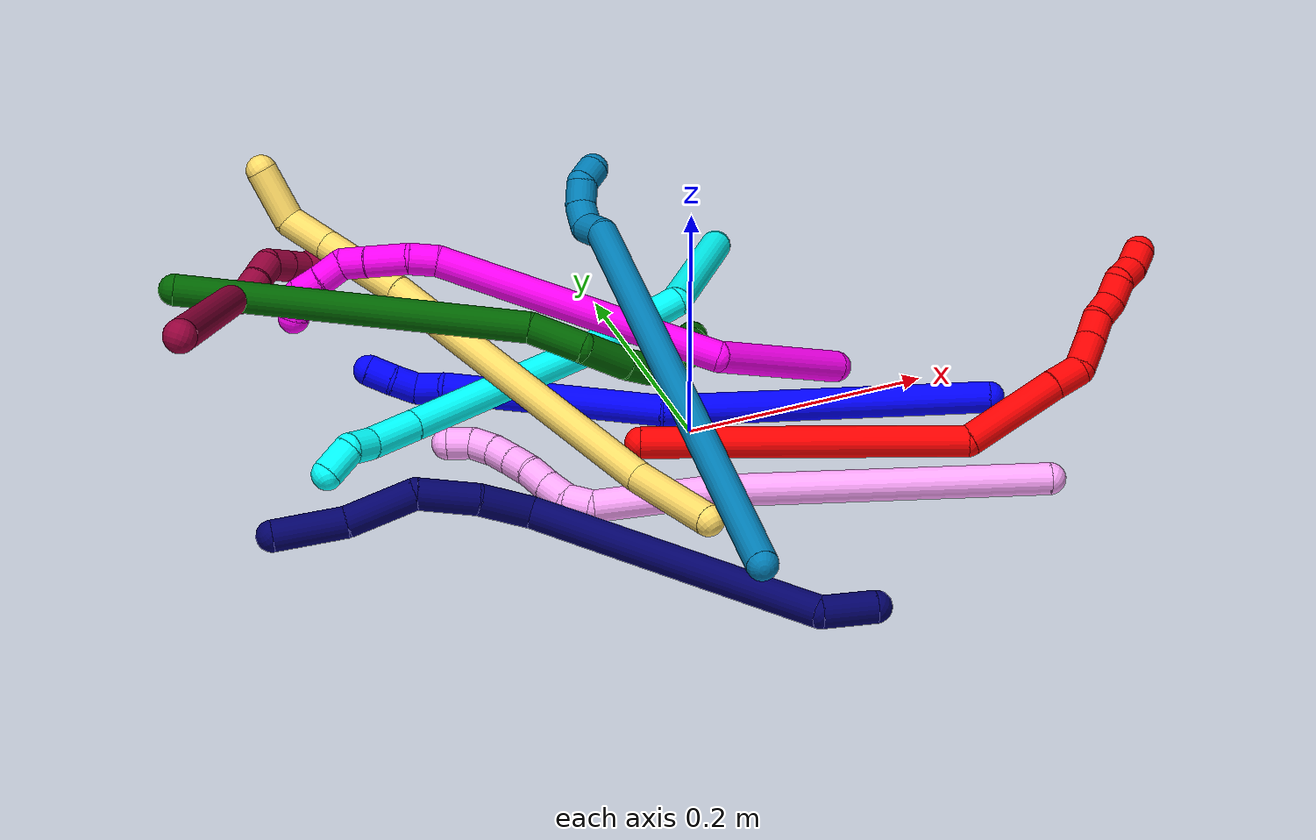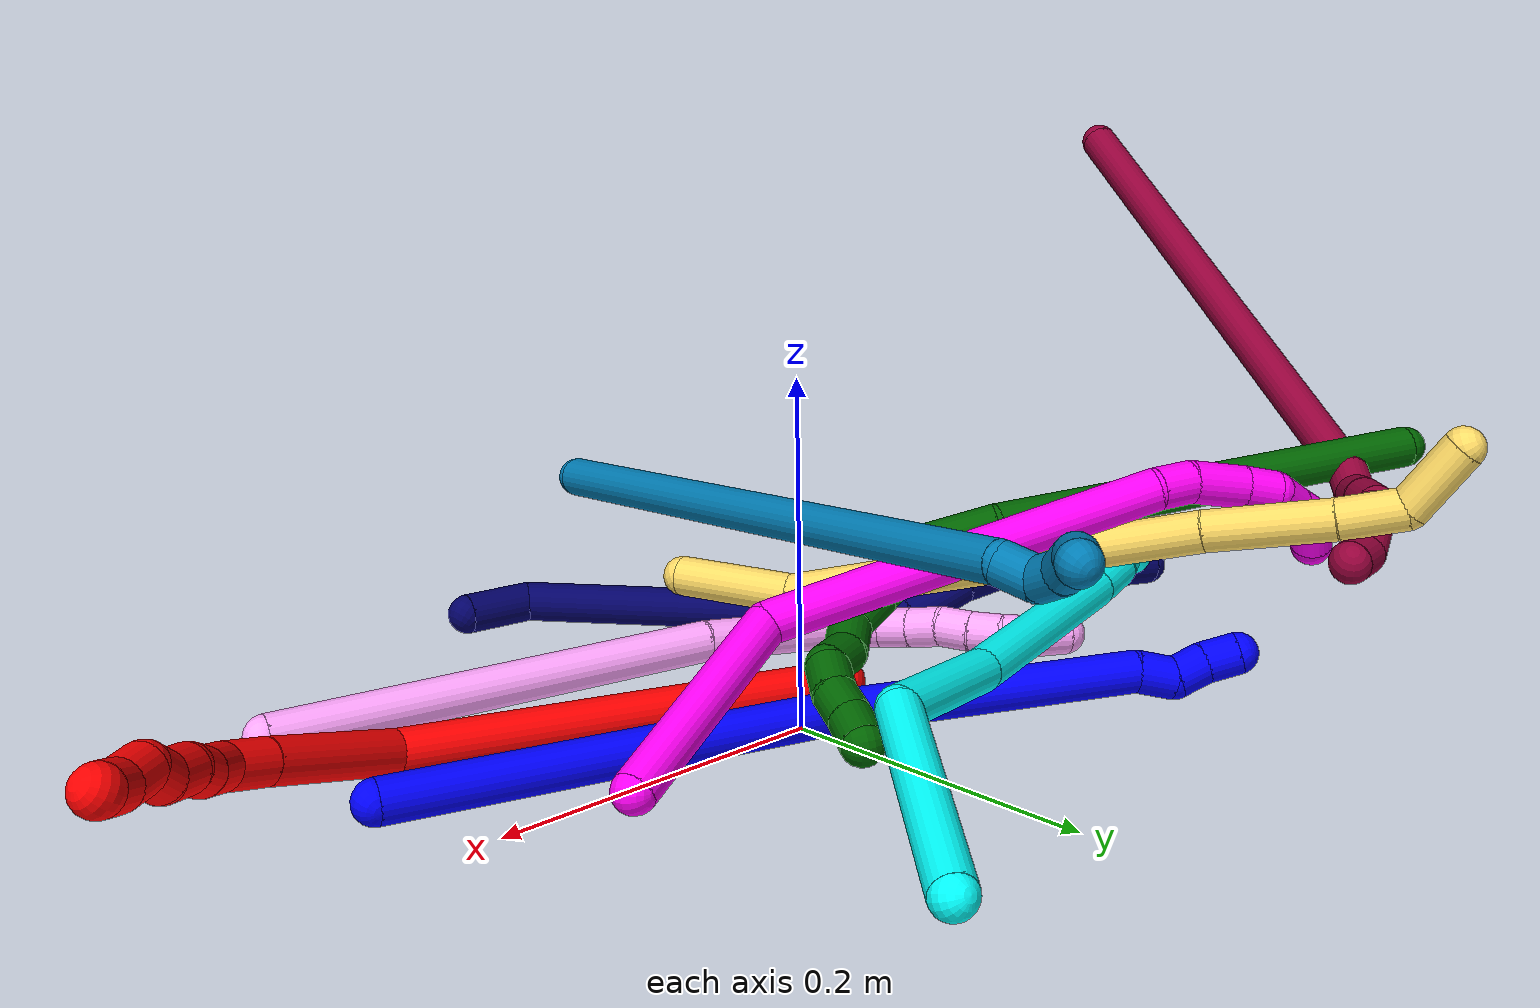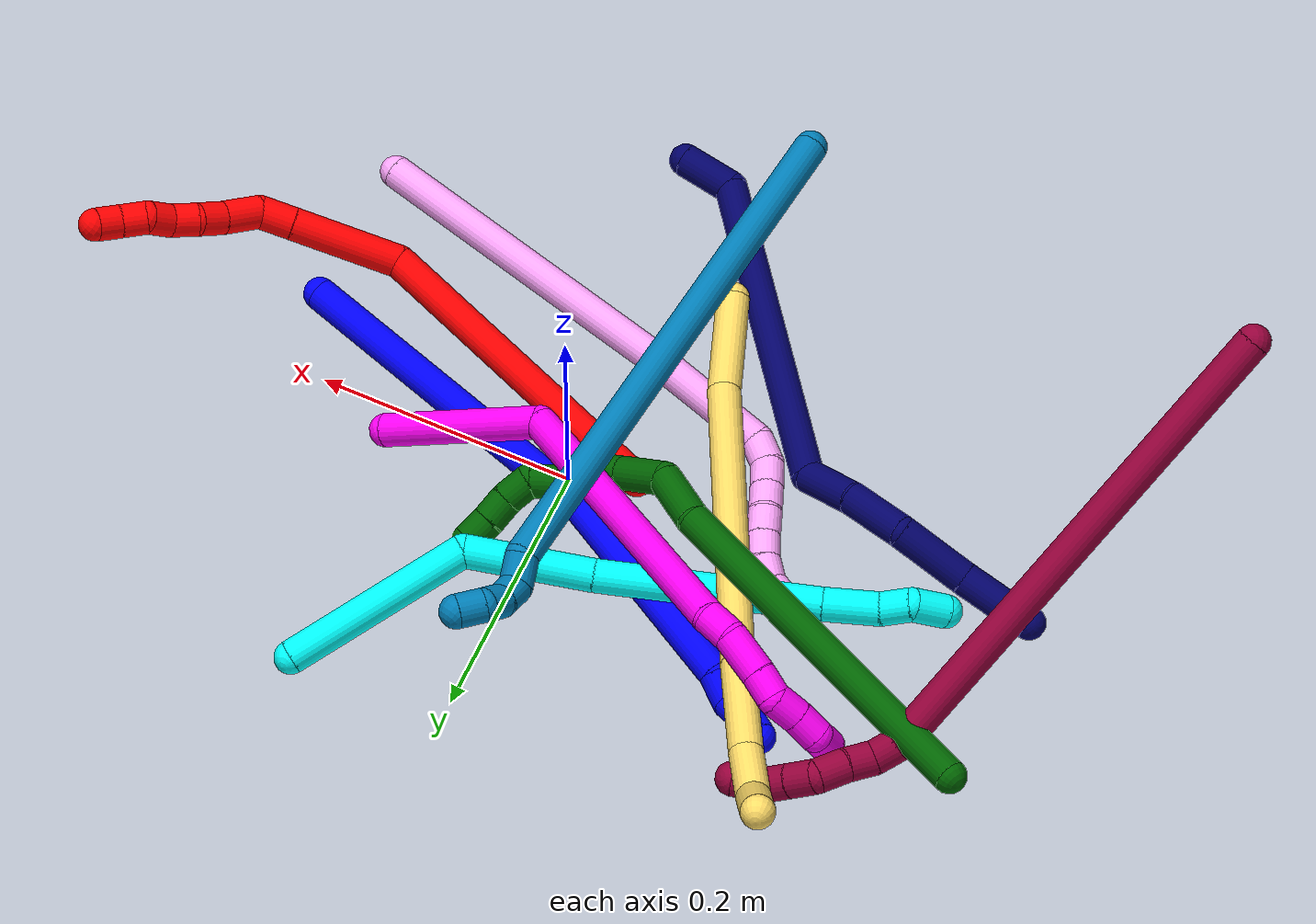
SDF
<sdf version="1.7">
 <world name="default">
  <plugin name="TubeGeneratorPlugin" filename="libtube_generator_plugin.so"/>
  <model name="photoneo_s_sensor">
   <static>1</static>
   <pose>0 0 2 1.57079 1.57079 3.14159</pose>
   <link name="link">
    <inertial><mass>0.1</mass></inertial>
    <sensor name="sensor" type="depth">
     <update_rate>30</update_rate>
     <camera>
      <horizontal_fov>1.22</horizontal_fov>
      <image><width>1920</width><height>1200</height><format>B8G8R8</format></image>
      <clip><near>0.1</near><far>4</far></clip>
      <depth_camera><output>points</output></depth_camera>
     </camera>
     <plugin name="camera_plugin" filename="libgazebo_ros_depth_camera.so">
      <baseline>0.2</baseline>
      <alwaysOn>1</alwaysOn>
      <updateRate>0.0</updateRate>
      <cameraName>camera_ir</cameraName>
      <imageTopicName>/camera/color/image_raw</imageTopicName>
      <cameraInfoTopicName>/camera/color/camera_info</cameraInfoTopicName>
      <depthImageTopicName>/camera/depth/image_raw</depthImageTopicName>
      <depthImageCameraInfoTopicName>/camera/depth/camera_info</depthImageCameraInfoTopicName>
      <pointCloudTopicName>/camera/depth/points</pointCloudTopicName>
      <frameName>fr_optical</frameName>
      <pointCloudCutoff>0.1</pointCloudCutoff>
      <pointCloudCutoffMax>2.0</pointCloudCutoffMax>
      <distortionK1>0</distortionK1>
      <distortionK2>0</distortionK2>
      <distortionK3>0</distortionK3>
      <distortionT1>0</distortionT1>
      <distortionT2>0</distortionT2>
      <CxPrime>0</CxPrime>
      <Cx>0</Cx>
      <Cy>0</Cy>
      <focalLength>0</focalLength>
      <hackBaseline>0</hackBaseline>
     </plugin>
    </sensor>
   </link>
  </model>
  <gravity>0 0 -9.8</gravity>
  <magnetic_field>6e-06 2.3e-05 -4.2e-05</magnetic_field>
  <atmosphere type="adiabatic"/>
  <physics name="default_physics" default="0" type="ode">
   <max_step_size>0.003</max_step_size>
   <real_time_factor>1</real_time_factor>
   <real_time_update_rate>1000</real_time_update_rate>
   <max_contacts>10000</max_contacts>
   <ode>
    <solver>
     <type>quick</type>
     <iters>100</iters>
     <sor>1.3</sor>
     <use_dynamic_moi_rescaling>0</use_dynamic_moi_rescaling>
    </solver>
    <constraints>
     <contact_max_correcting_vel>0</contact_max_correcting_vel>
     <contact_surface_layer>0.001</contact_surface_layer>
     <cfm>0</cfm>
     <erp>0.2</erp>
    </constraints>
   </ode>
  </physics>
  <scene><ambient>0.4 0.4 0.4 1</ambient><background>0.7 0.7 0.7 1</background><shadows>0</shadows></scene>
  <audio><device>default</device></audio>
  <spherical_coordinates>
   <surface_model>EARTH_WGS84</surface_model>
   <latitude_deg>0</latitude_deg>
   <longitude_deg>0</longitude_deg>
   <elevation>0</elevation>
   <heading_deg>0</heading_deg>
  </spherical_coordinates>
  <model name="bin">
   <static>1</static>
   <link name="bottom">
    <collision name="collision-bottom">
     <pose>0 0 -0.01 0 -0 0</pose>
     <geometry><box><size>0.8 0.6 0.02</size></box></geometry>
     <surface>
      <friction><ode><mu>100</mu><mu2>100</mu2></ode></friction>
      <contact><collide_bitmask>65535</collide_bitmask></contact>
     </surface>
    </collision>
   </link>
   <link name="west_wall">
    <collision name="collision-west_wall">
     <pose>-0.41 0 0.1 0 -0 0</pose>
     <geometry><box><size>0.02 0.6 0.2</size></box></geometry>
     <surface>
      <friction><ode><mu>100</mu><mu2>100</mu2></ode></friction>
      <contact><collide_bitmask>65535</collide_bitmask></contact>
     </surface>
    </collision>
   </link>
   <link name="east_wall">
    <collision name="collision-east_wall">
     <pose>0.41 0 0.1 0 -0 0</pose>
     <geometry><box><size>0.02 0.6 0.2</size></box></geometry>
     <surface>
      <friction><ode><mu>100</mu><mu2>100</mu2></ode></friction>
      <contact><collide_bitmask>65535</collide_bitmask></contact>
     </surface>
    </collision>
   </link>
   <link name="south_wall">
    <collision name="collision-south_wall">
     <pose>0 -0.31 0.1 0 -0 0</pose>
     <geometry><box><size>0.8 0.02 0.2</size></box></geometry>
     <surface>
      <friction><ode><mu>100</mu><mu2>100</mu2></ode></friction>
      <contact><collide_bitmask>65535</collide_bitmask></contact>
     </surface>
    </collision>
   </link>
   <link name="north_wall">
    <collision name="collision-north_wall">
     <pose>0 0.31 0.1 0 -0 0</pose>
     <geometry><box><size>0.8 0.02 0.2</size></box></geometry>
     <surface>
      <friction><ode><mu>100</mu><mu2>100</mu2></ode></friction>
      <contact><collide_bitmask>65535</collide_bitmask></contact>
     </surface>
    </collision>
   </link>
  </model>
  <model name="1">
   <static>0</static>
   <link name="1">
    <collision name="collision-cylinder-e_1_1_4">
     <pose>-0.117741 0.055267 -0.003864 -1.64059 -1.13099 1.1951</pose>
     <geometry><cylinder><radius>0.0125</radius><length>0.260248</length></cylinder></geometry>
     <surface>
      <friction><ode><mu>1.16</mu><mu2>1.16</mu2><slip1>0</slip1><slip2>0</slip2></ode></friction>
      <contact><ode><kp>1e+06</kp><kd>1</kd><max_vel>0</max_vel><min_depth>0.001</min_depth></ode></contact>
     </surface>
    </collision>
    <visual name="visual-cylinder-e_1_1_4">
     <pose>-0.117741 0.055267 -0.003864 -1.64059 -1.13099 1.1951</pose>
     <geometry><cylinder><radius>0.0125</radius><length>0.260248</length></cylinder></geometry>
     <material><ambient>0 0 1 1</ambient></material>
    </visual>
    <collision name="collision-cylinder-e_2_4_5">
     <pose>-0.310062 0.15118 -0.028153 -2.03646 -1.02309 1.47707</pose>
     <geometry><cylinder><radius>0.0125</radius><length>0.174716</length></cylinder></geometry>
     <surface>
      <friction><ode><mu>1.16</mu><mu2>1.16</mu2><slip1>0</slip1><slip2>0</slip2></ode></friction>
      <contact><ode><kp>1e+06</kp><kd>1</kd><max_vel>0</max_vel><min_depth>0.001</min_depth></ode></contact>
     </surface>
    </collision>
    <visual name="visual-cylinder-e_2_4_5">
     <pose>-0.310062 0.15118 -0.028153 -2.03646 -1.02309 1.47707</pose>
     <geometry><cylinder><radius>0.0125</radius><length>0.174716</length></cylinder></geometry>
     <material><ambient>0 0 1 1</ambient></material>
    </visual>
    <collision name="collision-cylinder-e_3_5_6">
     <pose>-0.39497 0.194431 -0.053467 -2.65199 -1.0786 2.35074</pose>
     <geometry><cylinder><radius>0.0125</radius><length>0.023441</length></cylinder></geometry>
     <surface>
      <friction><ode><mu>1.16</mu><mu2>1.16</mu2><slip1>0</slip1><slip2>0</slip2></ode></friction>
      <contact><ode><kp>1e+06</kp><kd>1</kd><max_vel>0</max_vel><min_depth>0.001</min_depth></ode></contact>
     </surface>
    </collision>
    <visual name="visual-cylinder-e_3_5_6">
     <pose>-0.39497 0.194431 -0.053467 -2.65199 -1.0786 2.35074</pose>
     <geometry><cylinder><radius>0.0125</radius><length>0.023441</length></cylinder></geometry>
     <material><ambient>0 0 1 1</ambient></material>
    </visual>
    <collision name="collision-cylinder-e_4_6_7">
     <pose>-0.412301 0.204464 -0.059637 -1.74171 -0.74854 0.872793</pose>
     <geometry><cylinder><radius>0.0125</radius><length>0.020575</length></cylinder></geometry>
     <surface>
      <friction><ode><mu>1.16</mu><mu2>1.16</mu2><slip1>0</slip1><slip2>0</slip2></ode></friction>
      <contact><ode><kp>1e+06</kp><kd>1</kd><max_vel>0</max_vel><min_depth>0.001</min_depth></ode></contact>
     </surface>
    </collision>
    <visual name="visual-cylinder-e_4_6_7">
     <pose>-0.412301 0.204464 -0.059637 -1.74171 -0.74854 0.872793</pose>
     <geometry><cylinder><radius>0.0125</radius><length>0.020575</length></cylinder></geometry>
     <material><ambient>0 0 1 1</ambient></material>
    </visual>
    <collision name="collision-cylinder-e_5_7_2">
     <pose>-0.426404 0.218659 -0.06469 -2.07919 -0.741875 1.16952</pose>
     <geometry><cylinder><radius>0.0125</radius><length>0.021019</length></cylinder></geometry>
     <surface>
      <friction><ode><mu>1.16</mu><mu2>1.16</mu2><slip1>0</slip1><slip2>0</slip2></ode></friction>
      <contact><ode><kp>1e+06</kp><kd>1</kd><max_vel>0</max_vel><min_depth>0.001</min_depth></ode></contact>
     </surface>
    </collision>
    <visual name="visual-cylinder-e_5_7_2">
     <pose>-0.426404 0.218659 -0.06469 -2.07919 -0.741875 1.16952</pose>
     <geometry><cylinder><radius>0.0125</radius><length>0.021019</length></cylinder></geometry>
     <material><ambient>0 0 1 1</ambient></material>
    </visual>
    <collision name="collision-sphere-2">
     <pose>-0.433505 0.225427 -0.068462 0 -0 0</pose>
     <geometry><sphere><radius>0.0125</radius></sphere></geometry>
     <surface>
      <friction><ode><mu>1.16</mu><mu2>1.16</mu2><slip1>0</slip1><slip2>0</slip2></ode></friction>
      <contact><ode><kp>1e+06</kp><kd>1</kd><max_vel>0</max_vel><min_depth>0.001</min_depth></ode></contact>
     </surface>
    </collision>
    <visual name="visual-sphere-2">
     <pose>-0.433505 0.225427 -0.068462 0 -0 0</pose>
     <geometry><sphere><radius>0.0125</radius></sphere></geometry>
     <material><ambient>0 0 1 1</ambient></material>
    </visual>
    <collision name="collision-sphere-7">
     <pose>-0.419303 0.211891 -0.060919 0 -0 0</pose>
     <geometry><sphere><radius>0.0125</radius></sphere></geometry>
     <surface>
      <friction><ode><mu>1.16</mu><mu2>1.16</mu2><slip1>0</slip1><slip2>0</slip2></ode></friction>
      <contact><ode><kp>1e+06</kp><kd>1</kd><max_vel>0</max_vel><min_depth>0.001</min_depth></ode></contact>
     </surface>
    </collision>
    <visual name="visual-sphere-7">
     <pose>-0.419303 0.211891 -0.060919 0 -0 0</pose>
     <geometry><sphere><radius>0.0125</radius></sphere></geometry>
     <material><ambient>0 0 1 1</ambient></material>
    </visual>
    <collision name="collision-sphere-6">
     <pose>-0.4053 0.197036 -0.058355 0 -0 0</pose>
     <geometry><sphere><radius>0.0125</radius></sphere></geometry>
     <surface>
      <friction><ode><mu>1.16</mu><mu2>1.16</mu2><slip1>0</slip1><slip2>0</slip2></ode></friction>
      <contact><ode><kp>1e+06</kp><kd>1</kd><max_vel>0</max_vel><min_depth>0.001</min_depth></ode></contact>
     </surface>
    </collision>
    <visual name="visual-sphere-6">
     <pose>-0.4053 0.197036 -0.058355 0 -0 0</pose>
     <geometry><sphere><radius>0.0125</radius></sphere></geometry>
     <material><ambient>0 0 1 1</ambient></material>
    </visual>
    <collision name="collision-sphere-5">
     <pose>-0.384641 0.191826 -0.048579 0 -0 0</pose>
     <geometry><sphere><radius>0.0125</radius></sphere></geometry>
     <surface>
      <friction><ode><mu>1.16</mu><mu2>1.16</mu2><slip1>0</slip1><slip2>0</slip2></ode></friction>
      <contact><ode><kp>1e+06</kp><kd>1</kd><max_vel>0</max_vel><min_depth>0.001</min_depth></ode></contact>
     </surface>
    </collision>
    <visual name="visual-sphere-5">
     <pose>-0.384641 0.191826 -0.048579 0 -0 0</pose>
     <geometry><sphere><radius>0.0125</radius></sphere></geometry>
     <material><ambient>0 0 1 1</ambient></material>
    </visual>
    <collision name="collision-sphere-1">
     <geometry><sphere><radius>0.0125</radius></sphere></geometry>
     <surface>
      <friction><ode><mu>1.16</mu><mu2>1.16</mu2><slip1>0</slip1><slip2>0</slip2></ode></friction>
      <contact><ode><kp>1e+06</kp><kd>1</kd><max_vel>0</max_vel><min_depth>0.001</min_depth></ode></contact>
     </surface>
    </collision>
    <visual name="visual-sphere-1">
     <geometry><sphere><radius>0.0125</radius></sphere></geometry>
     <material><ambient>0 0 1 1</ambient></material>
    </visual>
    <collision name="collision-sphere-4">
     <pose>-0.235482 0.110534 -0.007727 0 -0 0</pose>
     <geometry><sphere><radius>0.0125</radius></sphere></geometry>
     <surface>
      <friction><ode><mu>1.16</mu><mu2>1.16</mu2><slip1>0</slip1><slip2>0</slip2></ode></friction>
      <contact><ode><kp>1e+06</kp><kd>1</kd><max_vel>0</max_vel><min_depth>0.001</min_depth></ode></contact>
     </surface>
    </collision>
    <visual name="visual-sphere-4">
     <pose>-0.235482 0.110534 -0.007727 0 -0 0</pose>
     <geometry><sphere><radius>0.0125</radius></sphere></geometry>
     <material><ambient>0 0 1 1</ambient></material>
    </visual>
    <inertial>
     <pose>-0.223038 0.108315 -0.019529 0 -0 0</pose>
     <mass>0.5</mass>
     <inertia>
      <ixx>0.001042</ixx>
      <ixy>0</ixy>
      <ixz>0</ixz>
      <iyy>0.002371</iyy>
      <iyz>0</iyz>
      <izz>0.000881</izz>
     </inertia>
    </inertial>
   </link>
   <pose>0.232578 -0.059705 0.011514 1.42275 -0.430716 -0.217439</pose>
  </model>
  <model name="2">
   <static>0</static>
   <link name="2">
    <collision name="collision-cylinder-e_1_1_4">
     <pose>0.087213 -0.027423 0.090259 0.294961 0.746202 0.116172</pose>
     <geometry><cylinder><radius>0.0125</radius><length>0.256943</length></cylinder></geometry>
     <surface>
      <friction><ode><mu>1.16</mu><mu2>1.16</mu2><slip1>0</slip1><slip2>0</slip2></ode></friction>
      <contact><ode><kp>1e+06</kp><kd>1</kd><max_vel>0</max_vel><min_depth>0.001</min_depth></ode></contact>
     </surface>
    </collision>
    <visual name="visual-cylinder-e_1_1_4">
     <pose>0.087213 -0.027423 0.090259 0.294961 0.746202 0.116172</pose>
     <geometry><cylinder><radius>0.0125</radius><length>0.256943</length></cylinder></geometry>
     <material><ambient>1 0 0 1</ambient></material>
    </visual>
    <collision name="collision-cylinder-e_2_4_5">
     <pose>0.185858 -0.047618 0.220543 -0.178647 0.273996 -0.024693</pose>
     <geometry><cylinder><radius>0.0125</radius><length>0.084495</length></cylinder></geometry>
     <surface>
      <friction><ode><mu>1.16</mu><mu2>1.16</mu2><slip1>0</slip1><slip2>0</slip2></ode></friction>
      <contact><ode><kp>1e+06</kp><kd>1</kd><max_vel>0</max_vel><min_depth>0.001</min_depth></ode></contact>
     </surface>
    </collision>
    <visual name="visual-cylinder-e_2_4_5">
     <pose>0.185858 -0.047618 0.220543 -0.178647 0.273996 -0.024693</pose>
     <geometry><cylinder><radius>0.0125</radius><length>0.084495</length></cylinder></geometry>
     <material><ambient>1 0 0 1</ambient></material>
    </visual>
    <collision name="collision-cylinder-e_3_5_6">
     <pose>0.20141 -0.038132 0.272795 -0.182681 0.31995 -0.029556</pose>
     <geometry><cylinder><radius>0.0125</radius><length>0.0262</length></cylinder></geometry>
     <surface>
      <friction><ode><mu>1.16</mu><mu2>1.16</mu2><slip1>0</slip1><slip2>0</slip2></ode></friction>
      <contact><ode><kp>1e+06</kp><kd>1</kd><max_vel>0</max_vel><min_depth>0.001</min_depth></ode></contact>
     </surface>
    </collision>
    <visual name="visual-cylinder-e_3_5_6">
     <pose>0.20141 -0.038132 0.272795 -0.182681 0.31995 -0.029556</pose>
     <geometry><cylinder><radius>0.0125</radius><length>0.0262</length></cylinder></geometry>
     <material><ambient>1 0 0 1</ambient></material>
    </visual>
    <collision name="collision-cylinder-e_4_6_7">
     <pose>0.20346 -0.026987 0.297324 -0.625587 -0.13559 0.043912</pose>
     <geometry><cylinder><radius>0.0125</radius><length>0.03063</length></cylinder></geometry>
     <surface>
      <friction><ode><mu>1.16</mu><mu2>1.16</mu2><slip1>0</slip1><slip2>0</slip2></ode></friction>
      <contact><ode><kp>1e+06</kp><kd>1</kd><max_vel>0</max_vel><min_depth>0.001</min_depth></ode></contact>
     </surface>
    </collision>
    <visual name="visual-cylinder-e_4_6_7">
     <pose>0.20346 -0.026987 0.297324 -0.625587 -0.13559 0.043912</pose>
     <geometry><cylinder><radius>0.0125</radius><length>0.03063</length></cylinder></geometry>
     <material><ambient>1 0 0 1</ambient></material>
    </visual>
    <collision name="collision-cylinder-e_5_7_8">
     <pose>0.19883 -0.013101 0.318593 -0.508675 -0.244258 0.063795</pose>
     <geometry><cylinder><radius>0.0125</radius><length>0.021166</length></cylinder></geometry>
     <surface>
      <friction><ode><mu>1.16</mu><mu2>1.16</mu2><slip1>0</slip1><slip2>0</slip2></ode></friction>
      <contact><ode><kp>1e+06</kp><kd>1</kd><max_vel>0</max_vel><min_depth>0.001</min_depth></ode></contact>
     </surface>
    </collision>
    <visual name="visual-cylinder-e_5_7_8">
     <pose>0.19883 -0.013101 0.318593 -0.508675 -0.244258 0.063795</pose>
     <geometry><cylinder><radius>0.0125</radius><length>0.021166</length></cylinder></geometry>
     <material><ambient>1 0 0 1</ambient></material>
    </visual>
    <collision name="collision-cylinder-e_6_8_9">
     <pose>0.197306 -0.002762 0.336208 -0.553093 0.101506 -0.028832</pose>
     <geometry><cylinder><radius>0.0125</radius><length>0.020427</length></cylinder></geometry>
     <surface>
      <friction><ode><mu>1.16</mu><mu2>1.16</mu2><slip1>0</slip1><slip2>0</slip2></ode></friction>
      <contact><ode><kp>1e+06</kp><kd>1</kd><max_vel>0</max_vel><min_depth>0.001</min_depth></ode></contact>
     </surface>
    </collision>
    <visual name="visual-cylinder-e_6_8_9">
     <pose>0.197306 -0.002762 0.336208 -0.553093 0.101506 -0.028832</pose>
     <geometry><cylinder><radius>0.0125</radius><length>0.020427</length></cylinder></geometry>
     <material><ambient>1 0 0 1</ambient></material>
    </visual>
    <collision name="collision-cylinder-e_7_9_10">
     <pose>0.195664 0.005654 0.35399 -0.324962 -0.27085 0.044665</pose>
     <geometry><cylinder><radius>0.0125</radius><length>0.02001</length></cylinder></geometry>
     <surface>
      <friction><ode><mu>1.16</mu><mu2>1.16</mu2><slip1>0</slip1><slip2>0</slip2></ode></friction>
      <contact><ode><kp>1e+06</kp><kd>1</kd><max_vel>0</max_vel><min_depth>0.001</min_depth></ode></contact>
     </surface>
    </collision>
    <visual name="visual-cylinder-e_7_9_10">
     <pose>0.195664 0.005654 0.35399 -0.324962 -0.27085 0.044665</pose>
     <geometry><cylinder><radius>0.0125</radius><length>0.02001</length></cylinder></geometry>
     <material><ambient>1 0 0 1</ambient></material>
    </visual>
    <collision name="collision-cylinder-e_8_10_11">
     <pose>0.195365 0.014873 0.370696 -0.681514 0.239253 -0.085192</pose>
     <geometry><cylinder><radius>0.0125</radius><length>0.020069</length></cylinder></geometry>
     <surface>
      <friction><ode><mu>1.16</mu><mu2>1.16</mu2><slip1>0</slip1><slip2>0</slip2></ode></friction>
      <contact><ode><kp>1e+06</kp><kd>1</kd><max_vel>0</max_vel><min_depth>0.001</min_depth></ode></contact>
     </surface>
    </collision>
    <visual name="visual-cylinder-e_8_10_11">
     <pose>0.195365 0.014873 0.370696 -0.681514 0.239253 -0.085192</pose>
     <geometry><cylinder><radius>0.0125</radius><length>0.020069</length></cylinder></geometry>
     <material><ambient>1 0 0 1</ambient></material>
    </visual>
    <collision name="collision-cylinder-e_9_11_2">
     <pose>0.196678 0.0267 0.386462 -0.606543 -0.106381 0.033318</pose>
     <geometry><cylinder><radius>0.0125</radius><length>0.02006</length></cylinder></geometry>
     <surface>
      <friction><ode><mu>1.16</mu><mu2>1.16</mu2><slip1>0</slip1><slip2>0</slip2></ode></friction>
      <contact><ode><kp>1e+06</kp><kd>1</kd><max_vel>0</max_vel><min_depth>0.001</min_depth></ode></contact>
     </surface>
    </collision>
    <visual name="visual-cylinder-e_9_11_2">
     <pose>0.196678 0.0267 0.386462 -0.606543 -0.106381 0.033318</pose>
     <geometry><cylinder><radius>0.0125</radius><length>0.02006</length></cylinder></geometry>
     <material><ambient>1 0 0 1</ambient></material>
    </visual>
    <collision name="collision-sphere-2">
     <pose>0.195613 0.032385 0.394656 0 -0 0</pose>
     <geometry><sphere><radius>0.0125</radius></sphere></geometry>
     <surface>
      <friction><ode><mu>1.16</mu><mu2>1.16</mu2><slip1>0</slip1><slip2>0</slip2></ode></friction>
      <contact><ode><kp>1e+06</kp><kd>1</kd><max_vel>0</max_vel><min_depth>0.001</min_depth></ode></contact>
     </surface>
    </collision>
    <visual name="visual-sphere-2">
     <pose>0.195613 0.032385 0.394656 0 -0 0</pose>
     <geometry><sphere><radius>0.0125</radius></sphere></geometry>
     <material><ambient>1 0 0 1</ambient></material>
    </visual>
    <collision name="collision-sphere-11">
     <pose>0.197743 0.021015 0.378267 0 -0 0</pose>
     <geometry><sphere><radius>0.0125</radius></sphere></geometry>
     <surface>
      <friction><ode><mu>1.16</mu><mu2>1.16</mu2><slip1>0</slip1><slip2>0</slip2></ode></friction>
      <contact><ode><kp>1e+06</kp><kd>1</kd><max_vel>0</max_vel><min_depth>0.001</min_depth></ode></contact>
     </surface>
    </collision>
    <visual name="visual-sphere-11">
     <pose>0.197743 0.021015 0.378267 0 -0 0</pose>
     <geometry><sphere><radius>0.0125</radius></sphere></geometry>
     <material><ambient>1 0 0 1</ambient></material>
    </visual>
    <collision name="collision-sphere-10">
     <pose>0.192987 0.008732 0.363125 0 -0 0</pose>
     <geometry><sphere><radius>0.0125</radius></sphere></geometry>
     <surface>
      <friction><ode><mu>1.16</mu><mu2>1.16</mu2><slip1>0</slip1><slip2>0</slip2></ode></friction>
      <contact><ode><kp>1e+06</kp><kd>1</kd><max_vel>0</max_vel><min_depth>0.001</min_depth></ode></contact>
     </surface>
    </collision>
    <visual name="visual-sphere-10">
     <pose>0.192987 0.008732 0.363125 0 -0 0</pose>
     <geometry><sphere><radius>0.0125</radius></sphere></geometry>
     <material><ambient>1 0 0 1</ambient></material>
    </visual>
    <collision name="collision-sphere-9">
     <pose>0.198341 0.002576 0.344854 0 -0 0</pose>
     <geometry><sphere><radius>0.0125</radius></sphere></geometry>
     <surface>
      <friction><ode><mu>1.16</mu><mu2>1.16</mu2><slip1>0</slip1><slip2>0</slip2></ode></friction>
      <contact><ode><kp>1e+06</kp><kd>1</kd><max_vel>0</max_vel><min_depth>0.001</min_depth></ode></contact>
     </surface>
    </collision>
    <visual name="visual-sphere-9">
     <pose>0.198341 0.002576 0.344854 0 -0 0</pose>
     <geometry><sphere><radius>0.0125</radius></sphere></geometry>
     <material><ambient>1 0 0 1</ambient></material>
    </visual>
    <collision name="collision-sphere-4">
     <pose>0.174427 -0.054846 0.180518 0 -0 0</pose>
     <geometry><sphere><radius>0.0125</radius></sphere></geometry>
     <surface>
      <friction><ode><mu>1.16</mu><mu2>1.16</mu2><slip1>0</slip1><slip2>0</slip2></ode></friction>
      <contact><ode><kp>1e+06</kp><kd>1</kd><max_vel>0</max_vel><min_depth>0.001</min_depth></ode></contact>
     </surface>
    </collision>
    <visual name="visual-sphere-4">
     <pose>0.174427 -0.054846 0.180518 0 -0 0</pose>
     <geometry><sphere><radius>0.0125</radius></sphere></geometry>
     <material><ambient>1 0 0 1</ambient></material>
    </visual>
    <collision name="collision-sphere-1">
     <geometry><sphere><radius>0.0125</radius></sphere></geometry>
     <surface>
      <friction><ode><mu>1.16</mu><mu2>1.16</mu2><slip1>0</slip1><slip2>0</slip2></ode></friction>
      <contact><ode><kp>1e+06</kp><kd>1</kd><max_vel>0</max_vel><min_depth>0.001</min_depth></ode></contact>
     </surface>
    </collision>
    <visual name="visual-sphere-1">
     <geometry><sphere><radius>0.0125</radius></sphere></geometry>
     <material><ambient>1 0 0 1</ambient></material>
    </visual>
    <collision name="collision-sphere-8">
     <pose>0.196271 -0.0081 0.327562 0 -0 0</pose>
     <geometry><sphere><radius>0.0125</radius></sphere></geometry>
     <surface>
      <friction><ode><mu>1.16</mu><mu2>1.16</mu2><slip1>0</slip1><slip2>0</slip2></ode></friction>
      <contact><ode><kp>1e+06</kp><kd>1</kd><max_vel>0</max_vel><min_depth>0.001</min_depth></ode></contact>
     </surface>
    </collision>
    <visual name="visual-sphere-8">
     <pose>0.196271 -0.0081 0.327562 0 -0 0</pose>
     <geometry><sphere><radius>0.0125</radius></sphere></geometry>
     <material><ambient>1 0 0 1</ambient></material>
    </visual>
    <collision name="collision-sphere-5">
     <pose>0.197289 -0.040391 0.260567 0 -0 0</pose>
     <geometry><sphere><radius>0.0125</radius></sphere></geometry>
     <surface>
      <friction><ode><mu>1.16</mu><mu2>1.16</mu2><slip1>0</slip1><slip2>0</slip2></ode></friction>
      <contact><ode><kp>1e+06</kp><kd>1</kd><max_vel>0</max_vel><min_depth>0.001</min_depth></ode></contact>
     </surface>
    </collision>
    <visual name="visual-sphere-5">
     <pose>0.197289 -0.040391 0.260567 0 -0 0</pose>
     <geometry><sphere><radius>0.0125</radius></sphere></geometry>
     <material><ambient>1 0 0 1</ambient></material>
    </visual>
    <collision name="collision-sphere-6">
     <pose>0.20553 -0.035873 0.285023 0 -0 0</pose>
     <geometry><sphere><radius>0.0125</radius></sphere></geometry>
     <surface>
      <friction><ode><mu>1.16</mu><mu2>1.16</mu2><slip1>0</slip1><slip2>0</slip2></ode></friction>
      <contact><ode><kp>1e+06</kp><kd>1</kd><max_vel>0</max_vel><min_depth>0.001</min_depth></ode></contact>
     </surface>
    </collision>
    <visual name="visual-sphere-6">
     <pose>0.20553 -0.035873 0.285023 0 -0 0</pose>
     <geometry><sphere><radius>0.0125</radius></sphere></geometry>
     <material><ambient>1 0 0 1</ambient></material>
    </visual>
    <collision name="collision-sphere-7">
     <pose>0.201389 -0.018102 0.309625 0 -0 0</pose>
     <geometry><sphere><radius>0.0125</radius></sphere></geometry>
     <surface>
      <friction><ode><mu>1.16</mu><mu2>1.16</mu2><slip1>0</slip1><slip2>0</slip2></ode></friction>
      <contact><ode><kp>1e+06</kp><kd>1</kd><max_vel>0</max_vel><min_depth>0.001</min_depth></ode></contact>
     </surface>
    </collision>
    <visual name="visual-sphere-7">
     <pose>0.201389 -0.018102 0.309625 0 -0 0</pose>
     <geometry><sphere><radius>0.0125</radius></sphere></geometry>
     <material><ambient>1 0 0 1</ambient></material>
    </visual>
    <inertial>
     <pose>0.139284 -0.024564 0.187934 0 -0 0</pose>
     <mass>0.5</mass>
     <inertia>
      <ixx>0.001238</ixx>
      <ixy>0</ixy>
      <ixz>0</ixz>
      <iyy>0.001573</iyy>
      <iyz>0</iyz>
      <izz>-0.000661</izz>
     </inertia>
    </inertial>
   </link>
   <pose>-0.048083 -0.015275 0.011707 -0.629283 0.796995 -0.618082</pose>
  </model>
  <model name="3">
   <static>0</static>
   <link name="3">
    <collision name="collision-cylinder-e_1_1_4">
     <pose>-0.036401 -0.036555 -0.051548 2.52475 -0.522607 -1.3966</pose>
     <geometry><cylinder><radius>0.0125</radius><length>0.145856</length></cylinder></geometry>
     <surface>
      <friction><ode><mu>1.16</mu><mu2>1.16</mu2><slip1>0</slip1><slip2>0</slip2></ode></friction>
      <contact><ode><kp>1e+06</kp><kd>1</kd><max_vel>0</max_vel><min_depth>0.001</min_depth></ode></contact>
     </surface>
    </collision>
    <visual name="visual-cylinder-e_1_1_4">
     <pose>-0.036401 -0.036555 -0.051548 2.52475 -0.522607 -1.3966</pose>
     <geometry><cylinder><radius>0.0125</radius><length>0.145856</length></cylinder></geometry>
     <material><ambient>0.003922 1 0.996078 1</ambient></material>
    </visual>
    <collision name="collision-cylinder-e_2_4_5">
     <pose>-0.117354 -0.074444 -0.120733 3.0661 -1.19284 -3.03046</pose>
     <geometry><cylinder><radius>0.0125</radius><length>0.095869</length></cylinder></geometry>
     <surface>
      <friction><ode><mu>1.16</mu><mu2>1.16</mu2><slip1>0</slip1><slip2>0</slip2></ode></friction>
      <contact><ode><kp>1e+06</kp><kd>1</kd><max_vel>0</max_vel><min_depth>0.001</min_depth></ode></contact>
     </surface>
    </collision>
    <visual name="visual-cylinder-e_2_4_5">
     <pose>-0.117354 -0.074444 -0.120733 3.0661 -1.19284 -3.03046</pose>
     <geometry><cylinder><radius>0.0125</radius><length>0.095869</length></cylinder></geometry>
     <material><ambient>0.003922 1 0.996078 1</ambient></material>
    </visual>
    <collision name="collision-cylinder-e_3_5_6">
     <pose>-0.239205 -0.087384 -0.166798 2.75396 -1.1927 -2.57863</pose>
     <geometry><cylinder><radius>0.0125</radius><length>0.16635</length></cylinder></geometry>
     <surface>
      <friction><ode><mu>1.16</mu><mu2>1.16</mu2><slip1>0</slip1><slip2>0</slip2></ode></friction>
      <contact><ode><kp>1e+06</kp><kd>1</kd><max_vel>0</max_vel><min_depth>0.001</min_depth></ode></contact>
     </surface>
    </collision>
    <visual name="visual-cylinder-e_3_5_6">
     <pose>-0.239205 -0.087384 -0.166798 2.75396 -1.1927 -2.57863</pose>
     <geometry><cylinder><radius>0.0125</radius><length>0.16635</length></cylinder></geometry>
     <material><ambient>0.003922 1 0.996078 1</ambient></material>
    </visual>
    <collision name="collision-cylinder-e_4_6_7">
     <pose>-0.335735 -0.102725 -0.202728 2.67978 -1.15968 -2.45231</pose>
     <geometry><cylinder><radius>0.0125</radius><length>0.041954</length></cylinder></geometry>
     <surface>
      <friction><ode><mu>1.16</mu><mu2>1.16</mu2><slip1>0</slip1><slip2>0</slip2></ode></friction>
      <contact><ode><kp>1e+06</kp><kd>1</kd><max_vel>0</max_vel><min_depth>0.001</min_depth></ode></contact>
     </surface>
    </collision>
    <visual name="visual-cylinder-e_4_6_7">
     <pose>-0.335735 -0.102725 -0.202728 2.67978 -1.15968 -2.45231</pose>
     <geometry><cylinder><radius>0.0125</radius><length>0.041954</length></cylinder></geometry>
     <material><ambient>0.003922 1 0.996078 1</ambient></material>
    </visual>
    <collision name="collision-cylinder-e_5_7_8">
     <pose>-0.364437 -0.111561 -0.214371 2.25235 -0.964569 -1.66489</pose>
     <geometry><cylinder><radius>0.0125</radius><length>0.023055</length></cylinder></geometry>
     <surface>
      <friction><ode><mu>1.16</mu><mu2>1.16</mu2><slip1>0</slip1><slip2>0</slip2></ode></friction>
      <contact><ode><kp>1e+06</kp><kd>1</kd><max_vel>0</max_vel><min_depth>0.001</min_depth></ode></contact>
     </surface>
    </collision>
    <visual name="visual-cylinder-e_5_7_8">
     <pose>-0.364437 -0.111561 -0.214371 2.25235 -0.964569 -1.66489</pose>
     <geometry><cylinder><radius>0.0125</radius><length>0.023055</length></cylinder></geometry>
     <material><ambient>0.003922 1 0.996078 1</ambient></material>
    </visual>
    <collision name="collision-cylinder-e_6_8_2">
     <pose>-0.384521 -0.113597 -0.226201 -2.76236 -0.908147 2.39231</pose>
     <geometry><cylinder><radius>0.0125</radius><length>0.026917</length></cylinder></geometry>
     <surface>
      <friction><ode><mu>1.16</mu><mu2>1.16</mu2><slip1>0</slip1><slip2>0</slip2></ode></friction>
      <contact><ode><kp>1e+06</kp><kd>1</kd><max_vel>0</max_vel><min_depth>0.001</min_depth></ode></contact>
     </surface>
    </collision>
    <visual name="visual-cylinder-e_6_8_2">
     <pose>-0.384521 -0.113597 -0.226201 -2.76236 -0.908147 2.39231</pose>
     <geometry><cylinder><radius>0.0125</radius><length>0.026917</length></cylinder></geometry>
     <material><ambient>0.003922 1 0.996078 1</ambient></material>
    </visual>
    <collision name="collision-sphere-2">
     <pose>-0.395131 -0.110531 -0.233892 0 -0 0</pose>
     <geometry><sphere><radius>0.0125</radius></sphere></geometry>
     <surface>
      <friction><ode><mu>1.16</mu><mu2>1.16</mu2><slip1>0</slip1><slip2>0</slip2></ode></friction>
      <contact><ode><kp>1e+06</kp><kd>1</kd><max_vel>0</max_vel><min_depth>0.001</min_depth></ode></contact>
     </surface>
    </collision>
    <visual name="visual-sphere-2">
     <pose>-0.395131 -0.110531 -0.233892 0 -0 0</pose>
     <geometry><sphere><radius>0.0125</radius></sphere></geometry>
     <material><ambient>0.003922 1 0.996078 1</ambient></material>
    </visual>
    <collision name="collision-sphere-4">
     <pose>-0.072802 -0.07311 -0.103095 0 -0 0</pose>
     <geometry><sphere><radius>0.0125</radius></sphere></geometry>
     <surface>
      <friction><ode><mu>1.16</mu><mu2>1.16</mu2><slip1>0</slip1><slip2>0</slip2></ode></friction>
      <contact><ode><kp>1e+06</kp><kd>1</kd><max_vel>0</max_vel><min_depth>0.001</min_depth></ode></contact>
     </surface>
    </collision>
    <visual name="visual-sphere-4">
     <pose>-0.072802 -0.07311 -0.103095 0 -0 0</pose>
     <geometry><sphere><radius>0.0125</radius></sphere></geometry>
     <material><ambient>0.003922 1 0.996078 1</ambient></material>
    </visual>
    <collision name="collision-sphere-1">
     <geometry><sphere><radius>0.0125</radius></sphere></geometry>
     <surface>
      <friction><ode><mu>1.16</mu><mu2>1.16</mu2><slip1>0</slip1><slip2>0</slip2></ode></friction>
      <contact><ode><kp>1e+06</kp><kd>1</kd><max_vel>0</max_vel><min_depth>0.001</min_depth></ode></contact>
     </surface>
    </collision>
    <visual name="visual-sphere-1">
     <geometry><sphere><radius>0.0125</radius></sphere></geometry>
     <material><ambient>0.003922 1 0.996078 1</ambient></material>
    </visual>
    <collision name="collision-sphere-8">
     <pose>-0.373911 -0.116662 -0.218509 0 -0 0</pose>
     <geometry><sphere><radius>0.0125</radius></sphere></geometry>
     <surface>
      <friction><ode><mu>1.16</mu><mu2>1.16</mu2><slip1>0</slip1><slip2>0</slip2></ode></friction>
      <contact><ode><kp>1e+06</kp><kd>1</kd><max_vel>0</max_vel><min_depth>0.001</min_depth></ode></contact>
     </surface>
    </collision>
    <visual name="visual-sphere-8">
     <pose>-0.373911 -0.116662 -0.218509 0 -0 0</pose>
     <geometry><sphere><radius>0.0125</radius></sphere></geometry>
     <material><ambient>0.003922 1 0.996078 1</ambient></material>
    </visual>
    <collision name="collision-sphere-5">
     <pose>-0.161905 -0.075778 -0.138372 0 -0 0</pose>
     <geometry><sphere><radius>0.0125</radius></sphere></geometry>
     <surface>
      <friction><ode><mu>1.16</mu><mu2>1.16</mu2><slip1>0</slip1><slip2>0</slip2></ode></friction>
      <contact><ode><kp>1e+06</kp><kd>1</kd><max_vel>0</max_vel><min_depth>0.001</min_depth></ode></contact>
     </surface>
    </collision>
    <visual name="visual-sphere-5">
     <pose>-0.161905 -0.075778 -0.138372 0 -0 0</pose>
     <geometry><sphere><radius>0.0125</radius></sphere></geometry>
     <material><ambient>0.003922 1 0.996078 1</ambient></material>
    </visual>
    <collision name="collision-sphere-6">
     <pose>-0.316506 -0.09899 -0.195223 0 -0 0</pose>
     <geometry><sphere><radius>0.0125</radius></sphere></geometry>
     <surface>
      <friction><ode><mu>1.16</mu><mu2>1.16</mu2><slip1>0</slip1><slip2>0</slip2></ode></friction>
      <contact><ode><kp>1e+06</kp><kd>1</kd><max_vel>0</max_vel><min_depth>0.001</min_depth></ode></contact>
     </surface>
    </collision>
    <visual name="visual-sphere-6">
     <pose>-0.316506 -0.09899 -0.195223 0 -0 0</pose>
     <geometry><sphere><radius>0.0125</radius></sphere></geometry>
     <material><ambient>0.003922 1 0.996078 1</ambient></material>
    </visual>
    <collision name="collision-sphere-7">
     <pose>-0.354964 -0.10646 -0.210233 0 -0 0</pose>
     <geometry><sphere><radius>0.0125</radius></sphere></geometry>
     <surface>
      <friction><ode><mu>1.16</mu><mu2>1.16</mu2><slip1>0</slip1><slip2>0</slip2></ode></friction>
      <contact><ode><kp>1e+06</kp><kd>1</kd><max_vel>0</max_vel><min_depth>0.001</min_depth></ode></contact>
     </surface>
    </collision>
    <visual name="visual-sphere-7">
     <pose>-0.354964 -0.10646 -0.210233 0 -0 0</pose>
     <geometry><sphere><radius>0.0125</radius></sphere></geometry>
     <material><ambient>0.003922 1 0.996078 1</ambient></material>
    </visual>
    <inertial>
     <pose>-0.178378 -0.073889 -0.132752 0 -0 0</pose>
     <mass>0.5</mass>
     <inertia>
      <ixx>-0.000452</ixx>
      <ixy>0</ixy>
      <ixz>0</ixz>
      <iyy>0.000188</iyy>
      <iyz>0</iyz>
      <izz>0.000749</izz>
     </inertia>
    </inertial>
   </link>
   <pose>0.116493 0.222463 0.016316 -1.22686 -0.011565 -0.089395</pose>
  </model>
  <model name="4">
   <static>0</static>
   <link name="4">
    <collision name="collision-cylinder-e_1_1_4">
     <pose>-0.103382 0.060996 0.049483 -0.889233 -0.921092 0.464224</pose>
     <geometry><cylinder><radius>0.0125</radius><length>0.259669</length></cylinder></geometry>
     <surface>
      <friction><ode><mu>1.16</mu><mu2>1.16</mu2><slip1>0</slip1><slip2>0</slip2></ode></friction>
      <contact><ode><kp>1e+06</kp><kd>1</kd><max_vel>0</max_vel><min_depth>0.001</min_depth></ode></contact>
     </surface>
    </collision>
    <visual name="visual-cylinder-e_1_1_4">
     <pose>-0.103382 0.060996 0.049483 -0.889233 -0.921092 0.464224</pose>
     <geometry><cylinder><radius>0.0125</radius><length>0.259669</length></cylinder></geometry>
     <material><ambient>1 0.65098 0.996078 1</ambient></material>
    </visual>
    <collision name="collision-cylinder-e_2_4_5">
     <pose>-0.246682 0.139673 0.118801 -0.728056 -0.983481 0.402628</pose>
     <geometry><cylinder><radius>0.0125</radius><length>0.095904</length></cylinder></geometry>
     <surface>
      <friction><ode><mu>1.16</mu><mu2>1.16</mu2><slip1>0</slip1><slip2>0</slip2></ode></friction>
      <contact><ode><kp>1e+06</kp><kd>1</kd><max_vel>0</max_vel><min_depth>0.001</min_depth></ode></contact>
     </surface>
    </collision>
    <visual name="visual-cylinder-e_2_4_5">
     <pose>-0.246682 0.139673 0.118801 -0.728056 -0.983481 0.402628</pose>
     <geometry><cylinder><radius>0.0125</radius><length>0.095904</length></cylinder></geometry>
     <material><ambient>1 0.65098 0.996078 1</ambient></material>
    </visual>
    <collision name="collision-cylinder-e_3_5_6">
     <pose>-0.296958 0.160693 0.137931 -1.77904 -1.2526 1.4571</pose>
     <geometry><cylinder><radius>0.0125</radius><length>0.021812</length></cylinder></geometry>
     <surface>
      <friction><ode><mu>1.16</mu><mu2>1.16</mu2><slip1>0</slip1><slip2>0</slip2></ode></friction>
      <contact><ode><kp>1e+06</kp><kd>1</kd><max_vel>0</max_vel><min_depth>0.001</min_depth></ode></contact>
     </surface>
    </collision>
    <visual name="visual-cylinder-e_3_5_6">
     <pose>-0.296958 0.160693 0.137931 -1.77904 -1.2526 1.4571</pose>
     <geometry><cylinder><radius>0.0125</radius><length>0.021812</length></cylinder></geometry>
     <material><ambient>1 0.65098 0.996078 1</ambient></material>
    </visual>
    <collision name="collision-cylinder-e_4_6_7">
     <pose>-0.316571 0.166634 0.132184 -2.66499 -1.02089 2.32295</pose>
     <geometry><cylinder><radius>0.0125</radius><length>0.021711</length></cylinder></geometry>
     <surface>
      <friction><ode><mu>1.16</mu><mu2>1.16</mu2><slip1>0</slip1><slip2>0</slip2></ode></friction>
      <contact><ode><kp>1e+06</kp><kd>1</kd><max_vel>0</max_vel><min_depth>0.001</min_depth></ode></contact>
     </surface>
    </collision>
    <visual name="visual-cylinder-e_4_6_7">
     <pose>-0.316571 0.166634 0.132184 -2.66499 -1.02089 2.32295</pose>
     <geometry><cylinder><radius>0.0125</radius><length>0.021711</length></cylinder></geometry>
     <material><ambient>1 0.65098 0.996078 1</ambient></material>
    </visual>
    <collision name="collision-cylinder-e_5_7_8">
     <pose>-0.334164 0.172248 0.122037 -2.6088 -0.95275 2.1687</pose>
     <geometry><cylinder><radius>0.0125</radius><length>0.02046</length></cylinder></geometry>
     <surface>
      <friction><ode><mu>1.16</mu><mu2>1.16</mu2><slip1>0</slip1><slip2>0</slip2></ode></friction>
      <contact><ode><kp>1e+06</kp><kd>1</kd><max_vel>0</max_vel><min_depth>0.001</min_depth></ode></contact>
     </surface>
    </collision>
    <visual name="visual-cylinder-e_5_7_8">
     <pose>-0.334164 0.172248 0.122037 -2.6088 -0.95275 2.1687</pose>
     <geometry><cylinder><radius>0.0125</radius><length>0.02046</length></cylinder></geometry>
     <material><ambient>1 0.65098 0.996078 1</ambient></material>
    </visual>
    <collision name="collision-cylinder-e_6_8_9">
     <pose>-0.351563 0.176305 0.112374 -2.91586 -1.09441 2.77371</pose>
     <geometry><cylinder><radius>0.0125</radius><length>0.020393</length></cylinder></geometry>
     <surface>
      <friction><ode><mu>1.16</mu><mu2>1.16</mu2><slip1>0</slip1><slip2>0</slip2></ode></friction>
      <contact><ode><kp>1e+06</kp><kd>1</kd><max_vel>0</max_vel><min_depth>0.001</min_depth></ode></contact>
     </surface>
    </collision>
    <visual name="visual-cylinder-e_6_8_9">
     <pose>-0.351563 0.176305 0.112374 -2.91586 -1.09441 2.77371</pose>
     <geometry><cylinder><radius>0.0125</radius><length>0.020393</length></cylinder></geometry>
     <material><ambient>1 0.65098 0.996078 1</ambient></material>
    </visual>
    <collision name="collision-cylinder-e_7_9_10">
     <pose>-0.369634 0.179172 0.103853 -2.71114 -1.11995 2.47053</pose>
     <geometry><cylinder><radius>0.0125</radius><length>0.020022</length></cylinder></geometry>
     <surface>
      <friction><ode><mu>1.16</mu><mu2>1.16</mu2><slip1>0</slip1><slip2>0</slip2></ode></friction>
      <contact><ode><kp>1e+06</kp><kd>1</kd><max_vel>0</max_vel><min_depth>0.001</min_depth></ode></contact>
     </surface>
    </collision>
    <visual name="visual-cylinder-e_7_9_10">
     <pose>-0.369634 0.179172 0.103853 -2.71114 -1.11995 2.47053</pose>
     <geometry><cylinder><radius>0.0125</radius><length>0.020022</length></cylinder></geometry>
     <material><ambient>1 0.65098 0.996078 1</ambient></material>
    </visual>
    <collision name="collision-cylinder-e_8_10_11">
     <pose>-0.388143 0.183356 0.097821 -2.2893 -1.25145 2.01972</pose>
     <geometry><cylinder><radius>0.0125</radius><length>0.020007</length></cylinder></geometry>
     <surface>
      <friction><ode><mu>1.16</mu><mu2>1.16</mu2><slip1>0</slip1><slip2>0</slip2></ode></friction>
      <contact><ode><kp>1e+06</kp><kd>1</kd><max_vel>0</max_vel><min_depth>0.001</min_depth></ode></contact>
     </surface>
    </collision>
    <visual name="visual-cylinder-e_8_10_11">
     <pose>-0.388143 0.183356 0.097821 -2.2893 -1.25145 2.01972</pose>
     <geometry><cylinder><radius>0.0125</radius><length>0.020007</length></cylinder></geometry>
     <material><ambient>1 0.65098 0.996078 1</ambient></material>
    </visual>
    <collision name="collision-cylinder-e_9_11_2">
     <pose>-0.406494 0.189447 0.098573 -0.923141 -1.08514 0.58273</pose>
     <geometry><cylinder><radius>0.0125</radius><length>0.020021</length></cylinder></geometry>
     <surface>
      <friction><ode><mu>1.16</mu><mu2>1.16</mu2><slip1>0</slip1><slip2>0</slip2></ode></friction>
      <contact><ode><kp>1e+06</kp><kd>1</kd><max_vel>0</max_vel><min_depth>0.001</min_depth></ode></contact>
     </surface>
    </collision>
    <visual name="visual-cylinder-e_9_11_2">
     <pose>-0.406494 0.189447 0.098573 -0.923141 -1.08514 0.58273</pose>
     <geometry><cylinder><radius>0.0125</radius><length>0.020021</length></cylinder></geometry>
     <material><ambient>1 0.65098 0.996078 1</ambient></material>
    </visual>
    <collision name="collision-sphere-2">
     <pose>-0.415347 0.193174 0.101392 0 -0 0</pose>
     <geometry><sphere><radius>0.0125</radius></sphere></geometry>
     <surface>
      <friction><ode><mu>1.16</mu><mu2>1.16</mu2><slip1>0</slip1><slip2>0</slip2></ode></friction>
      <contact><ode><kp>1e+06</kp><kd>1</kd><max_vel>0</max_vel><min_depth>0.001</min_depth></ode></contact>
     </surface>
    </collision>
    <visual name="visual-sphere-2">
     <pose>-0.415347 0.193174 0.101392 0 -0 0</pose>
     <geometry><sphere><radius>0.0125</radius></sphere></geometry>
     <material><ambient>1 0.65098 0.996078 1</ambient></material>
    </visual>
    <collision name="collision-sphere-11">
     <pose>-0.397641 0.185721 0.095754 0 -0 0</pose>
     <geometry><sphere><radius>0.0125</radius></sphere></geometry>
     <surface>
      <friction><ode><mu>1.16</mu><mu2>1.16</mu2><slip1>0</slip1><slip2>0</slip2></ode></friction>
      <contact><ode><kp>1e+06</kp><kd>1</kd><max_vel>0</max_vel><min_depth>0.001</min_depth></ode></contact>
     </surface>
    </collision>
    <visual name="visual-sphere-11">
     <pose>-0.397641 0.185721 0.095754 0 -0 0</pose>
     <geometry><sphere><radius>0.0125</radius></sphere></geometry>
     <material><ambient>1 0.65098 0.996078 1</ambient></material>
    </visual>
    <collision name="collision-sphere-10">
     <pose>-0.378645 0.180992 0.099888 0 -0 0</pose>
     <geometry><sphere><radius>0.0125</radius></sphere></geometry>
     <surface>
      <friction><ode><mu>1.16</mu><mu2>1.16</mu2><slip1>0</slip1><slip2>0</slip2></ode></friction>
      <contact><ode><kp>1e+06</kp><kd>1</kd><max_vel>0</max_vel><min_depth>0.001</min_depth></ode></contact>
     </surface>
    </collision>
    <visual name="visual-sphere-10">
     <pose>-0.378645 0.180992 0.099888 0 -0 0</pose>
     <geometry><sphere><radius>0.0125</radius></sphere></geometry>
     <material><ambient>1 0.65098 0.996078 1</ambient></material>
    </visual>
    <collision name="collision-sphere-9">
     <pose>-0.360624 0.177352 0.107817 0 -0 0</pose>
     <geometry><sphere><radius>0.0125</radius></sphere></geometry>
     <surface>
      <friction><ode><mu>1.16</mu><mu2>1.16</mu2><slip1>0</slip1><slip2>0</slip2></ode></friction>
      <contact><ode><kp>1e+06</kp><kd>1</kd><max_vel>0</max_vel><min_depth>0.001</min_depth></ode></contact>
     </surface>
    </collision>
    <visual name="visual-sphere-9">
     <pose>-0.360624 0.177352 0.107817 0 -0 0</pose>
     <geometry><sphere><radius>0.0125</radius></sphere></geometry>
     <material><ambient>1 0.65098 0.996078 1</ambient></material>
    </visual>
    <collision name="collision-sphere-4">
     <pose>-0.206765 0.121992 0.098966 0 -0 0</pose>
     <geometry><sphere><radius>0.0125</radius></sphere></geometry>
     <surface>
      <friction><ode><mu>1.16</mu><mu2>1.16</mu2><slip1>0</slip1><slip2>0</slip2></ode></friction>
      <contact><ode><kp>1e+06</kp><kd>1</kd><max_vel>0</max_vel><min_depth>0.001</min_depth></ode></contact>
     </surface>
    </collision>
    <visual name="visual-sphere-4">
     <pose>-0.206765 0.121992 0.098966 0 -0 0</pose>
     <geometry><sphere><radius>0.0125</radius></sphere></geometry>
     <material><ambient>1 0.65098 0.996078 1</ambient></material>
    </visual>
    <collision name="collision-sphere-1">
     <geometry><sphere><radius>0.0125</radius></sphere></geometry>
     <surface>
      <friction><ode><mu>1.16</mu><mu2>1.16</mu2><slip1>0</slip1><slip2>0</slip2></ode></friction>
      <contact><ode><kp>1e+06</kp><kd>1</kd><max_vel>0</max_vel><min_depth>0.001</min_depth></ode></contact>
     </surface>
    </collision>
    <visual name="visual-sphere-1">
     <geometry><sphere><radius>0.0125</radius></sphere></geometry>
     <material><ambient>1 0.65098 0.996078 1</ambient></material>
    </visual>
    <collision name="collision-sphere-8">
     <pose>-0.342502 0.175259 0.116931 0 -0 0</pose>
     <geometry><sphere><radius>0.0125</radius></sphere></geometry>
     <surface>
      <friction><ode><mu>1.16</mu><mu2>1.16</mu2><slip1>0</slip1><slip2>0</slip2></ode></friction>
      <contact><ode><kp>1e+06</kp><kd>1</kd><max_vel>0</max_vel><min_depth>0.001</min_depth></ode></contact>
     </surface>
    </collision>
    <visual name="visual-sphere-8">
     <pose>-0.342502 0.175259 0.116931 0 -0 0</pose>
     <geometry><sphere><radius>0.0125</radius></sphere></geometry>
     <material><ambient>1 0.65098 0.996078 1</ambient></material>
    </visual>
    <collision name="collision-sphere-5">
     <pose>-0.286599 0.157355 0.138636 0 -0 0</pose>
     <geometry><sphere><radius>0.0125</radius></sphere></geometry>
     <surface>
      <friction><ode><mu>1.16</mu><mu2>1.16</mu2><slip1>0</slip1><slip2>0</slip2></ode></friction>
      <contact><ode><kp>1e+06</kp><kd>1</kd><max_vel>0</max_vel><min_depth>0.001</min_depth></ode></contact>
     </surface>
    </collision>
    <visual name="visual-sphere-5">
     <pose>-0.286599 0.157355 0.138636 0 -0 0</pose>
     <geometry><sphere><radius>0.0125</radius></sphere></geometry>
     <material><ambient>1 0.65098 0.996078 1</ambient></material>
    </visual>
    <collision name="collision-sphere-6">
     <pose>-0.307316 0.164031 0.137225 0 -0 0</pose>
     <geometry><sphere><radius>0.0125</radius></sphere></geometry>
     <surface>
      <friction><ode><mu>1.16</mu><mu2>1.16</mu2><slip1>0</slip1><slip2>0</slip2></ode></friction>
      <contact><ode><kp>1e+06</kp><kd>1</kd><max_vel>0</max_vel><min_depth>0.001</min_depth></ode></contact>
     </surface>
    </collision>
    <visual name="visual-sphere-6">
     <pose>-0.307316 0.164031 0.137225 0 -0 0</pose>
     <geometry><sphere><radius>0.0125</radius></sphere></geometry>
     <material><ambient>1 0.65098 0.996078 1</ambient></material>
    </visual>
    <collision name="collision-sphere-7">
     <pose>-0.325827 0.169237 0.127143 0 -0 0</pose>
     <geometry><sphere><radius>0.0125</radius></sphere></geometry>
     <surface>
      <friction><ode><mu>1.16</mu><mu2>1.16</mu2><slip1>0</slip1><slip2>0</slip2></ode></friction>
      <contact><ode><kp>1e+06</kp><kd>1</kd><max_vel>0</max_vel><min_depth>0.001</min_depth></ode></contact>
     </surface>
    </collision>
    <visual name="visual-sphere-7">
     <pose>-0.325827 0.169237 0.127143 0 -0 0</pose>
     <geometry><sphere><radius>0.0125</radius></sphere></geometry>
     <material><ambient>1 0.65098 0.996078 1</ambient></material>
    </visual>
    <inertial>
     <pose>-0.20233 0.109051 0.081839 0 -0 0</pose>
     <mass>0.5</mass>
     <inertia>
      <ixx>0.001218</ixx>
      <ixy>0</ixy>
      <ixz>0</ixz>
      <iyy>0.001747</iyy>
      <iyz>0</iyz>
      <izz>0.00053</izz>
     </inertia>
    </inertial>
   </link>
   <pose>0.227272 -0.17906 0.011543 1.94375 -0.319996 -0.828923</pose>
  </model>
  <model name="5">
   <static>0</static>
   <link name="5">
    <collision name="collision-cylinder-e_1_1_4">
     <pose>0.004664 0.018795 0.033951 -0.505586 0.119616 -0.030934</pose>
     <geometry><cylinder><radius>0.0125</radius><length>0.078171</length></cylinder></geometry>
     <surface>
      <friction><ode><mu>1.16</mu><mu2>1.16</mu2><slip1>0</slip1><slip2>0</slip2></ode></friction>
      <contact><ode><kp>1e+06</kp><kd>1</kd><max_vel>0</max_vel><min_depth>0.001</min_depth></ode></contact>
     </surface>
    </collision>
    <visual name="visual-cylinder-e_1_1_4">
     <pose>0.004664 0.018795 0.033951 -0.505586 0.119616 -0.030934</pose>
     <geometry><cylinder><radius>0.0125</radius><length>0.078171</length></cylinder></geometry>
     <material><ambient>1 0.858824 0.4 1</ambient></material>
    </visual>
    <collision name="collision-cylinder-e_2_4_5">
     <pose>-0.00127 0.075848 0.192187 -0.298628 -0.081321 0.01224</pose>
     <geometry><cylinder><radius>0.0125</radius><length>0.260942</length></cylinder></geometry>
     <surface>
      <friction><ode><mu>1.16</mu><mu2>1.16</mu2><slip1>0</slip1><slip2>0</slip2></ode></friction>
      <contact><ode><kp>1e+06</kp><kd>1</kd><max_vel>0</max_vel><min_depth>0.001</min_depth></ode></contact>
     </surface>
    </collision>
    <visual name="visual-cylinder-e_2_4_5">
     <pose>-0.00127 0.075848 0.192187 -0.298628 -0.081321 0.01224</pose>
     <geometry><cylinder><radius>0.0125</radius><length>0.260942</length></cylinder></geometry>
     <material><ambient>1 0.858824 0.4 1</ambient></material>
    </visual>
    <collision name="collision-cylinder-e_3_5_6">
     <pose>-0.015346 0.12812 0.351333 -0.382195 -0.0923 0.017869</pose>
     <geometry><cylinder><radius>0.0125</radius><length>0.075466</length></cylinder></geometry>
     <surface>
      <friction><ode><mu>1.16</mu><mu2>1.16</mu2><slip1>0</slip1><slip2>0</slip2></ode></friction>
      <contact><ode><kp>1e+06</kp><kd>1</kd><max_vel>0</max_vel><min_depth>0.001</min_depth></ode></contact>
     </surface>
    </collision>
    <visual name="visual-cylinder-e_3_5_6">
     <pose>-0.015346 0.12812 0.351333 -0.382195 -0.0923 0.017869</pose>
     <geometry><cylinder><radius>0.0125</radius><length>0.075466</length></cylinder></geometry>
     <material><ambient>1 0.858824 0.4 1</ambient></material>
    </visual>
    <collision name="collision-cylinder-e_4_6_7">
     <pose>-0.021985 0.148795 0.404604 -0.347214 -0.160091 0.028134</pose>
     <geometry><cylinder><radius>0.0125</radius><length>0.039663</length></cylinder></geometry>
     <surface>
      <friction><ode><mu>1.16</mu><mu2>1.16</mu2><slip1>0</slip1><slip2>0</slip2></ode></friction>
      <contact><ode><kp>1e+06</kp><kd>1</kd><max_vel>0</max_vel><min_depth>0.001</min_depth></ode></contact>
     </surface>
    </collision>
    <visual name="visual-cylinder-e_4_6_7">
     <pose>-0.021985 0.148795 0.404604 -0.347214 -0.160091 0.028134</pose>
     <geometry><cylinder><radius>0.0125</radius><length>0.039663</length></cylinder></geometry>
     <material><ambient>1 0.858824 0.4 1</ambient></material>
    </visual>
    <collision name="collision-cylinder-e_5_7_2">
     <pose>-0.032021 0.147799 0.443447 0.358557 -0.305156 -0.05572</pose>
     <geometry><cylinder><radius>0.0125</radius><length>0.045758</length></cylinder></geometry>
     <surface>
      <friction><ode><mu>1.16</mu><mu2>1.16</mu2><slip1>0</slip1><slip2>0</slip2></ode></friction>
      <contact><ode><kp>1e+06</kp><kd>1</kd><max_vel>0</max_vel><min_depth>0.001</min_depth></ode></contact>
     </surface>
    </collision>
    <visual name="visual-cylinder-e_5_7_2">
     <pose>-0.032021 0.147799 0.443447 0.358557 -0.305156 -0.05572</pose>
     <geometry><cylinder><radius>0.0125</radius><length>0.045758</length></cylinder></geometry>
     <material><ambient>1 0.858824 0.4 1</ambient></material>
    </visual>
    <collision name="collision-sphere-2">
     <pose>-0.038894 0.140141 0.463882 0 -0 0</pose>
     <geometry><sphere><radius>0.0125</radius></sphere></geometry>
     <surface>
      <friction><ode><mu>1.16</mu><mu2>1.16</mu2><slip1>0</slip1><slip2>0</slip2></ode></friction>
      <contact><ode><kp>1e+06</kp><kd>1</kd><max_vel>0</max_vel><min_depth>0.001</min_depth></ode></contact>
     </surface>
    </collision>
    <visual name="visual-sphere-2">
     <pose>-0.038894 0.140141 0.463882 0 -0 0</pose>
     <geometry><sphere><radius>0.0125</radius></sphere></geometry>
     <material><ambient>1 0.858824 0.4 1</ambient></material>
    </visual>
    <collision name="collision-sphere-7">
     <pose>-0.025147 0.155457 0.423013 0 -0 0</pose>
     <geometry><sphere><radius>0.0125</radius></sphere></geometry>
     <surface>
      <friction><ode><mu>1.16</mu><mu2>1.16</mu2><slip1>0</slip1><slip2>0</slip2></ode></friction>
      <contact><ode><kp>1e+06</kp><kd>1</kd><max_vel>0</max_vel><min_depth>0.001</min_depth></ode></contact>
     </surface>
    </collision>
    <visual name="visual-sphere-7">
     <pose>-0.025147 0.155457 0.423013 0 -0 0</pose>
     <geometry><sphere><radius>0.0125</radius></sphere></geometry>
     <material><ambient>1 0.858824 0.4 1</ambient></material>
    </visual>
    <collision name="collision-sphere-6">
     <pose>-0.018824 0.142133 0.386194 0 -0 0</pose>
     <geometry><sphere><radius>0.0125</radius></sphere></geometry>
     <surface>
      <friction><ode><mu>1.16</mu><mu2>1.16</mu2><slip1>0</slip1><slip2>0</slip2></ode></friction>
      <contact><ode><kp>1e+06</kp><kd>1</kd><max_vel>0</max_vel><min_depth>0.001</min_depth></ode></contact>
     </surface>
    </collision>
    <visual name="visual-sphere-6">
     <pose>-0.018824 0.142133 0.386194 0 -0 0</pose>
     <geometry><sphere><radius>0.0125</radius></sphere></geometry>
     <material><ambient>1 0.858824 0.4 1</ambient></material>
    </visual>
    <collision name="collision-sphere-5">
     <pose>-0.011869 0.114107 0.316471 0 -0 0</pose>
     <geometry><sphere><radius>0.0125</radius></sphere></geometry>
     <surface>
      <friction><ode><mu>1.16</mu><mu2>1.16</mu2><slip1>0</slip1><slip2>0</slip2></ode></friction>
      <contact><ode><kp>1e+06</kp><kd>1</kd><max_vel>0</max_vel><min_depth>0.001</min_depth></ode></contact>
     </surface>
    </collision>
    <visual name="visual-sphere-5">
     <pose>-0.011869 0.114107 0.316471 0 -0 0</pose>
     <geometry><sphere><radius>0.0125</radius></sphere></geometry>
     <material><ambient>1 0.858824 0.4 1</ambient></material>
    </visual>
    <collision name="collision-sphere-1">
     <geometry><sphere><radius>0.0125</radius></sphere></geometry>
     <surface>
      <friction><ode><mu>1.16</mu><mu2>1.16</mu2><slip1>0</slip1><slip2>0</slip2></ode></friction>
      <contact><ode><kp>1e+06</kp><kd>1</kd><max_vel>0</max_vel><min_depth>0.001</min_depth></ode></contact>
     </surface>
    </collision>
    <visual name="visual-sphere-1">
     <geometry><sphere><radius>0.0125</radius></sphere></geometry>
     <material><ambient>1 0.858824 0.4 1</ambient></material>
    </visual>
    <collision name="collision-sphere-4">
     <pose>0.009328 0.037589 0.067902 0 -0 0</pose>
     <geometry><sphere><radius>0.0125</radius></sphere></geometry>
     <surface>
      <friction><ode><mu>1.16</mu><mu2>1.16</mu2><slip1>0</slip1><slip2>0</slip2></ode></friction>
      <contact><ode><kp>1e+06</kp><kd>1</kd><max_vel>0</max_vel><min_depth>0.001</min_depth></ode></contact>
     </surface>
    </collision>
    <visual name="visual-sphere-4">
     <pose>0.009328 0.037589 0.067902 0 -0 0</pose>
     <geometry><sphere><radius>0.0125</radius></sphere></geometry>
     <material><ambient>1 0.858824 0.4 1</ambient></material>
    </visual>
    <inertial>
     <pose>-0.006924 0.087189 0.231313 0 -0 0</pose>
     <mass>0.5</mass>
     <inertia>
      <ixx>0.001597</ixx>
      <ixy>0</ixy>
      <ixz>0</ixz>
      <iyy>0.001542</iyy>
      <iyz>0</iyz>
      <izz>-0.000311</izz>
     </inertia>
    </inertial>
   </link>
   <pose>-0.055548 -0.168976 0.041129 -1.04791 0.348537 0.459965</pose>
  </model>
  <model name="6">
   <static>0</static>
   <link name="6">
    <collision name="collision-cylinder-e_1_1_4">
     <pose>0.0043 0.00117 -0.138822 -3.13316 0.030966 -2.61009</pose>
     <geometry><cylinder><radius>0.0125</radius><length>0.277787</length></cylinder></geometry>
     <surface>
      <friction><ode><mu>1.16</mu><mu2>1.16</mu2><slip1>0</slip1><slip2>0</slip2></ode></friction>
      <contact><ode><kp>1e+06</kp><kd>1</kd><max_vel>0</max_vel><min_depth>0.001</min_depth></ode></contact>
     </surface>
    </collision>
    <visual name="visual-cylinder-e_1_1_4">
     <pose>0.0043 0.00117 -0.138822 -3.13316 0.030966 -2.61009</pose>
     <geometry><cylinder><radius>0.0125</radius><length>0.277787</length></cylinder></geometry>
     <material><ambient>0 0.392157 0.003922 1</ambient></material>
    </visual>
    <collision name="collision-cylinder-e_2_4_5">
     <pose>0.004166 0.005529 -0.299307 -2.99547 -0.199812 1.8802</pose>
     <geometry><cylinder><radius>0.0125</radius><length>0.044682</length></cylinder></geometry>
     <surface>
      <friction><ode><mu>1.16</mu><mu2>1.16</mu2><slip1>0</slip1><slip2>0</slip2></ode></friction>
      <contact><ode><kp>1e+06</kp><kd>1</kd><max_vel>0</max_vel><min_depth>0.001</min_depth></ode></contact>
     </surface>
    </collision>
    <visual name="visual-cylinder-e_2_4_5">
     <pose>0.004166 0.005529 -0.299307 -2.99547 -0.199812 1.8802</pose>
     <geometry><cylinder><radius>0.0125</radius><length>0.044682</length></cylinder></geometry>
     <material><ambient>0 0.392157 0.003922 1</ambient></material>
    </visual>
    <collision name="collision-cylinder-e_3_5_6">
     <pose>0.005296 0.019363 -0.33755 -2.57078 0.275241 -0.882011</pose>
     <geometry><cylinder><radius>0.0125</radius><length>0.040949</length></cylinder></geometry>
     <surface>
      <friction><ode><mu>1.16</mu><mu2>1.16</mu2><slip1>0</slip1><slip2>0</slip2></ode></friction>
      <contact><ode><kp>1e+06</kp><kd>1</kd><max_vel>0</max_vel><min_depth>0.001</min_depth></ode></contact>
     </surface>
    </collision>
    <visual name="visual-cylinder-e_3_5_6">
     <pose>0.005296 0.019363 -0.33755 -2.57078 0.275241 -0.882011</pose>
     <geometry><cylinder><radius>0.0125</radius><length>0.040949</length></cylinder></geometry>
     <material><ambient>0 0.392157 0.003922 1</ambient></material>
    </visual>
    <collision name="collision-cylinder-e_4_6_7">
     <pose>0.015694 0.03552 -0.364545 -2.65497 0.389293 -1.34239</pose>
     <geometry><cylinder><radius>0.0125</radius><length>0.025471</length></cylinder></geometry>
     <surface>
      <friction><ode><mu>1.16</mu><mu2>1.16</mu2><slip1>0</slip1><slip2>0</slip2></ode></friction>
      <contact><ode><kp>1e+06</kp><kd>1</kd><max_vel>0</max_vel><min_depth>0.001</min_depth></ode></contact>
     </surface>
    </collision>
    <visual name="visual-cylinder-e_4_6_7">
     <pose>0.015694 0.03552 -0.364545 -2.65497 0.389293 -1.34239</pose>
     <geometry><cylinder><radius>0.0125</radius><length>0.025471</length></cylinder></geometry>
     <material><ambient>0 0.392157 0.003922 1</ambient></material>
    </visual>
    <collision name="collision-cylinder-e_5_7_8">
     <pose>0.031439 0.046176 -0.380243 -2.36928 0.976396 -1.83482</pose>
     <geometry><cylinder><radius>0.0125</radius><length>0.02634</length></cylinder></geometry>
     <surface>
      <friction><ode><mu>1.16</mu><mu2>1.16</mu2><slip1>0</slip1><slip2>0</slip2></ode></friction>
      <contact><ode><kp>1e+06</kp><kd>1</kd><max_vel>0</max_vel><min_depth>0.001</min_depth></ode></contact>
     </surface>
    </collision>
    <visual name="visual-cylinder-e_5_7_8">
     <pose>0.031439 0.046176 -0.380243 -2.36928 0.976396 -1.83482</pose>
     <geometry><cylinder><radius>0.0125</radius><length>0.02634</length></cylinder></geometry>
     <material><ambient>0 0.392157 0.003922 1</ambient></material>
    </visual>
    <collision name="collision-cylinder-e_6_8_9">
     <pose>0.050896 0.051881 -0.393166 -3.06865 0.839982 -2.97853</pose>
     <geometry><cylinder><radius>0.0125</radius><length>0.022954</length></cylinder></geometry>
     <surface>
      <friction><ode><mu>1.16</mu><mu2>1.16</mu2><slip1>0</slip1><slip2>0</slip2></ode></friction>
      <contact><ode><kp>1e+06</kp><kd>1</kd><max_vel>0</max_vel><min_depth>0.001</min_depth></ode></contact>
     </surface>
    </collision>
    <visual name="visual-cylinder-e_6_8_9">
     <pose>0.050896 0.051881 -0.393166 -3.06865 0.839982 -2.97853</pose>
     <geometry><cylinder><radius>0.0125</radius><length>0.022954</length></cylinder></geometry>
     <material><ambient>0 0.392157 0.003922 1</ambient></material>
    </visual>
    <collision name="collision-cylinder-e_7_9_10">
     <pose>0.068584 0.057821 -0.402086 -1.80419 1.02663 -1.23938</pose>
     <geometry><cylinder><radius>0.0125</radius><length>0.021371</length></cylinder></geometry>
     <surface>
      <friction><ode><mu>1.16</mu><mu2>1.16</mu2><slip1>0</slip1><slip2>0</slip2></ode></friction>
      <contact><ode><kp>1e+06</kp><kd>1</kd><max_vel>0</max_vel><min_depth>0.001</min_depth></ode></contact>
     </surface>
    </collision>
    <visual name="visual-cylinder-e_7_9_10">
     <pose>0.068584 0.057821 -0.402086 -1.80419 1.02663 -1.23938</pose>
     <geometry><cylinder><radius>0.0125</radius><length>0.021371</length></cylinder></geometry>
     <material><ambient>0 0.392157 0.003922 1</ambient></material>
    </visual>
    <collision name="collision-cylinder-e_8_10_11">
     <pose>0.086595 0.068039 -0.402219 -1.33809 1.06002 -0.867716</pose>
     <geometry><cylinder><radius>0.0125</radius><length>0.020332</length></cylinder></geometry>
     <surface>
      <friction><ode><mu>1.16</mu><mu2>1.16</mu2><slip1>0</slip1><slip2>0</slip2></ode></friction>
      <contact><ode><kp>1e+06</kp><kd>1</kd><max_vel>0</max_vel><min_depth>0.001</min_depth></ode></contact>
     </surface>
    </collision>
    <visual name="visual-cylinder-e_8_10_11">
     <pose>0.086595 0.068039 -0.402219 -1.33809 1.06002 -0.867716</pose>
     <geometry><cylinder><radius>0.0125</radius><length>0.020332</length></cylinder></geometry>
     <material><ambient>0 0.392157 0.003922 1</ambient></material>
    </visual>
    <collision name="collision-cylinder-e_9_11_2">
     <pose>0.104345 0.077591 -0.400891 -1.53229 1.08234 -1.04865</pose>
     <geometry><cylinder><radius>0.0125</radius><length>0.020114</length></cylinder></geometry>
     <surface>
      <friction><ode><mu>1.16</mu><mu2>1.16</mu2><slip1>0</slip1><slip2>0</slip2></ode></friction>
      <contact><ode><kp>1e+06</kp><kd>1</kd><max_vel>0</max_vel><min_depth>0.001</min_depth></ode></contact>
     </surface>
    </collision>
    <visual name="visual-cylinder-e_9_11_2">
     <pose>0.104345 0.077591 -0.400891 -1.53229 1.08234 -1.04865</pose>
     <geometry><cylinder><radius>0.0125</radius><length>0.020114</length></cylinder></geometry>
     <material><ambient>0 0.392157 0.003922 1</ambient></material>
    </visual>
    <collision name="collision-sphere-2">
     <pose>0.113225 0.082306 -0.40071 0 -0 0</pose>
     <geometry><sphere><radius>0.0125</radius></sphere></geometry>
     <surface>
      <friction><ode><mu>1.16</mu><mu2>1.16</mu2><slip1>0</slip1><slip2>0</slip2></ode></friction>
      <contact><ode><kp>1e+06</kp><kd>1</kd><max_vel>0</max_vel><min_depth>0.001</min_depth></ode></contact>
     </surface>
    </collision>
    <visual name="visual-sphere-2">
     <pose>0.113225 0.082306 -0.40071 0 -0 0</pose>
     <geometry><sphere><radius>0.0125</radius></sphere></geometry>
     <material><ambient>0 0.392157 0.003922 1</ambient></material>
    </visual>
    <collision name="collision-sphere-11">
     <pose>0.095464 0.072875 -0.401073 0 -0 0</pose>
     <geometry><sphere><radius>0.0125</radius></sphere></geometry>
     <surface>
      <friction><ode><mu>1.16</mu><mu2>1.16</mu2><slip1>0</slip1><slip2>0</slip2></ode></friction>
      <contact><ode><kp>1e+06</kp><kd>1</kd><max_vel>0</max_vel><min_depth>0.001</min_depth></ode></contact>
     </surface>
    </collision>
    <visual name="visual-sphere-11">
     <pose>0.095464 0.072875 -0.401073 0 -0 0</pose>
     <geometry><sphere><radius>0.0125</radius></sphere></geometry>
     <material><ambient>0 0.392157 0.003922 1</ambient></material>
    </visual>
    <collision name="collision-sphere-10">
     <pose>0.077727 0.063203 -0.403365 0 -0 0</pose>
     <geometry><sphere><radius>0.0125</radius></sphere></geometry>
     <surface>
      <friction><ode><mu>1.16</mu><mu2>1.16</mu2><slip1>0</slip1><slip2>0</slip2></ode></friction>
      <contact><ode><kp>1e+06</kp><kd>1</kd><max_vel>0</max_vel><min_depth>0.001</min_depth></ode></contact>
     </surface>
    </collision>
    <visual name="visual-sphere-10">
     <pose>0.077727 0.063203 -0.403365 0 -0 0</pose>
     <geometry><sphere><radius>0.0125</radius></sphere></geometry>
     <material><ambient>0 0.392157 0.003922 1</ambient></material>
    </visual>
    <collision name="collision-sphere-9">
     <pose>0.059442 0.052439 -0.400806 0 -0 0</pose>
     <geometry><sphere><radius>0.0125</radius></sphere></geometry>
     <surface>
      <friction><ode><mu>1.16</mu><mu2>1.16</mu2><slip1>0</slip1><slip2>0</slip2></ode></friction>
      <contact><ode><kp>1e+06</kp><kd>1</kd><max_vel>0</max_vel><min_depth>0.001</min_depth></ode></contact>
     </surface>
    </collision>
    <visual name="visual-sphere-9">
     <pose>0.059442 0.052439 -0.400806 0 -0 0</pose>
     <geometry><sphere><radius>0.0125</radius></sphere></geometry>
     <material><ambient>0 0.392157 0.003922 1</ambient></material>
    </visual>
    <collision name="collision-sphere-4">
     <pose>0.0086 0.00234 -0.277644 0 -0 0</pose>
     <geometry><sphere><radius>0.0125</radius></sphere></geometry>
     <surface>
      <friction><ode><mu>1.16</mu><mu2>1.16</mu2><slip1>0</slip1><slip2>0</slip2></ode></friction>
      <contact><ode><kp>1e+06</kp><kd>1</kd><max_vel>0</max_vel><min_depth>0.001</min_depth></ode></contact>
     </surface>
    </collision>
    <visual name="visual-sphere-4">
     <pose>0.0086 0.00234 -0.277644 0 -0 0</pose>
     <geometry><sphere><radius>0.0125</radius></sphere></geometry>
     <material><ambient>0 0.392157 0.003922 1</ambient></material>
    </visual>
    <collision name="collision-sphere-1">
     <geometry><sphere><radius>0.0125</radius></sphere></geometry>
     <surface>
      <friction><ode><mu>1.16</mu><mu2>1.16</mu2><slip1>0</slip1><slip2>0</slip2></ode></friction>
      <contact><ode><kp>1e+06</kp><kd>1</kd><max_vel>0</max_vel><min_depth>0.001</min_depth></ode></contact>
     </surface>
    </collision>
    <visual name="visual-sphere-1">
     <geometry><sphere><radius>0.0125</radius></sphere></geometry>
     <material><ambient>0 0.392157 0.003922 1</ambient></material>
    </visual>
    <collision name="collision-sphere-8">
     <pose>0.04235 0.051323 -0.385526 0 -0 0</pose>
     <geometry><sphere><radius>0.0125</radius></sphere></geometry>
     <surface>
      <friction><ode><mu>1.16</mu><mu2>1.16</mu2><slip1>0</slip1><slip2>0</slip2></ode></friction>
      <contact><ode><kp>1e+06</kp><kd>1</kd><max_vel>0</max_vel><min_depth>0.001</min_depth></ode></contact>
     </surface>
    </collision>
    <visual name="visual-sphere-8">
     <pose>0.04235 0.051323 -0.385526 0 -0 0</pose>
     <geometry><sphere><radius>0.0125</radius></sphere></geometry>
     <material><ambient>0 0.392157 0.003922 1</ambient></material>
    </visual>
    <collision name="collision-sphere-5">
     <pose>-0.000268 0.008717 -0.32097 0 -0 0</pose>
     <geometry><sphere><radius>0.0125</radius></sphere></geometry>
     <surface>
      <friction><ode><mu>1.16</mu><mu2>1.16</mu2><slip1>0</slip1><slip2>0</slip2></ode></friction>
      <contact><ode><kp>1e+06</kp><kd>1</kd><max_vel>0</max_vel><min_depth>0.001</min_depth></ode></contact>
     </surface>
    </collision>
    <visual name="visual-sphere-5">
     <pose>-0.000268 0.008717 -0.32097 0 -0 0</pose>
     <geometry><sphere><radius>0.0125</radius></sphere></geometry>
     <material><ambient>0 0.392157 0.003922 1</ambient></material>
    </visual>
    <collision name="collision-sphere-6">
     <pose>0.010861 0.03001 -0.354131 0 -0 0</pose>
     <geometry><sphere><radius>0.0125</radius></sphere></geometry>
     <surface>
      <friction><ode><mu>1.16</mu><mu2>1.16</mu2><slip1>0</slip1><slip2>0</slip2></ode></friction>
      <contact><ode><kp>1e+06</kp><kd>1</kd><max_vel>0</max_vel><min_depth>0.001</min_depth></ode></contact>
     </surface>
    </collision>
    <visual name="visual-sphere-6">
     <pose>0.010861 0.03001 -0.354131 0 -0 0</pose>
     <geometry><sphere><radius>0.0125</radius></sphere></geometry>
     <material><ambient>0 0.392157 0.003922 1</ambient></material>
    </visual>
    <collision name="collision-sphere-7">
     <pose>0.020528 0.04103 -0.37496 0 -0 0</pose>
     <geometry><sphere><radius>0.0125</radius></sphere></geometry>
     <surface>
      <friction><ode><mu>1.16</mu><mu2>1.16</mu2><slip1>0</slip1><slip2>0</slip2></ode></friction>
      <contact><ode><kp>1e+06</kp><kd>1</kd><max_vel>0</max_vel><min_depth>0.001</min_depth></ode></contact>
     </surface>
    </collision>
    <visual name="visual-sphere-7">
     <pose>0.020528 0.04103 -0.37496 0 -0 0</pose>
     <geometry><sphere><radius>0.0125</radius></sphere></geometry>
     <material><ambient>0 0.392157 0.003922 1</ambient></material>
    </visual>
    <inertial>
     <pose>0.018638 0.017713 -0.237838 0 -0 0</pose>
     <mass>0.5</mass>
     <inertia>
      <ixx>-0.002451</ixx>
      <ixy>0</ixy>
      <ixz>0</ixz>
      <iyy>0.00065</iyy>
      <iyz>0</iyz>
      <izz>-0.00012</izz>
     </inertia>
    </inertial>
   </link>
   <pose>-0.367623 0.160477 0.125947 -1.48972 -0.127214 1.08109</pose>
  </model>
  <model name="7">
   <static>0</static>
   <link name="7">
    <collision name="collision-cylinder-e_1_1_4">
     <pose>-0.006939 0.014068 -0.013889 -2.34976 -0.33755 0.774181</pose>
     <geometry><cylinder><radius>0.0125</radius><length>0.041903</length></cylinder></geometry>
     <surface>
      <friction><ode><mu>1.16</mu><mu2>1.16</mu2><slip1>0</slip1><slip2>0</slip2></ode></friction>
      <contact><ode><kp>1e+06</kp><kd>1</kd><max_vel>0</max_vel><min_depth>0.001</min_depth></ode></contact>
     </surface>
    </collision>
    <visual name="visual-cylinder-e_1_1_4">
     <pose>-0.006939 0.014068 -0.013889 -2.34976 -0.33755 0.774181</pose>
     <geometry><cylinder><radius>0.0125</radius><length>0.041903</length></cylinder></geometry>
     <material><ambient>0.003922 0 0.403922 1</ambient></material>
    </visual>
    <collision name="collision-cylinder-e_2_4_5">
     <pose>-0.122983 0.063015 -0.079798 -2.55097 -1.04968 2.17408</pose>
     <geometry><cylinder><radius>0.0125</radius><length>0.25161</length></cylinder></geometry>
     <surface>
      <friction><ode><mu>1.16</mu><mu2>1.16</mu2><slip1>0</slip1><slip2>0</slip2></ode></friction>
      <contact><ode><kp>1e+06</kp><kd>1</kd><max_vel>0</max_vel><min_depth>0.001</min_depth></ode></contact>
     </surface>
    </collision>
    <visual name="visual-cylinder-e_2_4_5">
     <pose>-0.122983 0.063015 -0.079798 -2.55097 -1.04968 2.17408</pose>
     <geometry><cylinder><radius>0.0125</radius><length>0.25161</length></cylinder></geometry>
     <material><ambient>0.003922 0 0.403922 1</ambient></material>
    </visual>
    <collision name="collision-cylinder-e_3_5_6">
     <pose>-0.239246 0.106395 -0.150675 -2.71802 -0.333096 1.32714</pose>
     <geometry><cylinder><radius>0.0125</radius><length>0.043774</length></cylinder></geometry>
     <surface>
      <friction><ode><mu>1.16</mu><mu2>1.16</mu2><slip1>0</slip1><slip2>0</slip2></ode></friction>
      <contact><ode><kp>1e+06</kp><kd>1</kd><max_vel>0</max_vel><min_depth>0.001</min_depth></ode></contact>
     </surface>
    </collision>
    <visual name="visual-cylinder-e_3_5_6">
     <pose>-0.239246 0.106395 -0.150675 -2.71802 -0.333096 1.32714</pose>
     <geometry><cylinder><radius>0.0125</radius><length>0.043774</length></cylinder></geometry>
     <material><ambient>0.003922 0 0.403922 1</ambient></material>
    </visual>
    <collision name="collision-cylinder-e_4_6_7">
     <pose>-0.256109 0.127629 -0.187753 -2.5317 -0.411705 1.17146</pose>
     <geometry><cylinder><radius>0.0125</radius><length>0.048514</length></cylinder></geometry>
     <surface>
      <friction><ode><mu>1.16</mu><mu2>1.16</mu2><slip1>0</slip1><slip2>0</slip2></ode></friction>
      <contact><ode><kp>1e+06</kp><kd>1</kd><max_vel>0</max_vel><min_depth>0.001</min_depth></ode></contact>
     </surface>
    </collision>
    <visual name="visual-cylinder-e_4_6_7">
     <pose>-0.256109 0.127629 -0.187753 -2.5317 -0.411705 1.17146</pose>
     <geometry><cylinder><radius>0.0125</radius><length>0.048514</length></cylinder></geometry>
     <material><ambient>0.003922 0 0.403922 1</ambient></material>
    </visual>
    <collision name="collision-cylinder-e_5_7_8">
     <pose>-0.274829 0.164801 -0.217141 -1.99934 -0.323656 0.497612</pose>
     <geometry><cylinder><radius>0.0125</radius><length>0.056679</length></cylinder></geometry>
     <surface>
      <friction><ode><mu>1.16</mu><mu2>1.16</mu2><slip1>0</slip1><slip2>0</slip2></ode></friction>
      <contact><ode><kp>1e+06</kp><kd>1</kd><max_vel>0</max_vel><min_depth>0.001</min_depth></ode></contact>
     </surface>
    </collision>
    <visual name="visual-cylinder-e_5_7_8">
     <pose>-0.274829 0.164801 -0.217141 -1.99934 -0.323656 0.497612</pose>
     <geometry><cylinder><radius>0.0125</radius><length>0.056679</length></cylinder></geometry>
     <material><ambient>0.003922 0 0.403922 1</ambient></material>
    </visual>
    <collision name="collision-cylinder-e_6_8_2">
     <pose>-0.293894 0.210505 -0.244856 -2.23213 -0.357031 0.707113</pose>
     <geometry><cylinder><radius>0.0125</radius><length>0.057521</length></cylinder></geometry>
     <surface>
      <friction><ode><mu>1.16</mu><mu2>1.16</mu2><slip1>0</slip1><slip2>0</slip2></ode></friction>
      <contact><ode><kp>1e+06</kp><kd>1</kd><max_vel>0</max_vel><min_depth>0.001</min_depth></ode></contact>
     </surface>
    </collision>
    <visual name="visual-cylinder-e_6_8_2">
     <pose>-0.293894 0.210505 -0.244856 -2.23213 -0.357031 0.707113</pose>
     <geometry><cylinder><radius>0.0125</radius><length>0.057521</length></cylinder></geometry>
     <material><ambient>0.003922 0 0.403922 1</ambient></material>
    </visual>
    <collision name="collision-sphere-2">
     <pose>-0.303945 0.23177 -0.261405 0 -0 0</pose>
     <geometry><sphere><radius>0.0125</radius></sphere></geometry>
     <surface>
      <friction><ode><mu>1.16</mu><mu2>1.16</mu2><slip1>0</slip1><slip2>0</slip2></ode></friction>
      <contact><ode><kp>1e+06</kp><kd>1</kd><max_vel>0</max_vel><min_depth>0.001</min_depth></ode></contact>
     </surface>
    </collision>
    <visual name="visual-sphere-2">
     <pose>-0.303945 0.23177 -0.261405 0 -0 0</pose>
     <geometry><sphere><radius>0.0125</radius></sphere></geometry>
     <material><ambient>0.003922 0 0.403922 1</ambient></material>
    </visual>
    <collision name="collision-sphere-4">
     <pose>-0.013877 0.028137 -0.027777 0 -0 0</pose>
     <geometry><sphere><radius>0.0125</radius></sphere></geometry>
     <surface>
      <friction><ode><mu>1.16</mu><mu2>1.16</mu2><slip1>0</slip1><slip2>0</slip2></ode></friction>
      <contact><ode><kp>1e+06</kp><kd>1</kd><max_vel>0</max_vel><min_depth>0.001</min_depth></ode></contact>
     </surface>
    </collision>
    <visual name="visual-sphere-4">
     <pose>-0.013877 0.028137 -0.027777 0 -0 0</pose>
     <geometry><sphere><radius>0.0125</radius></sphere></geometry>
     <material><ambient>0.003922 0 0.403922 1</ambient></material>
    </visual>
    <collision name="collision-sphere-1">
     <geometry><sphere><radius>0.0125</radius></sphere></geometry>
     <surface>
      <friction><ode><mu>1.16</mu><mu2>1.16</mu2><slip1>0</slip1><slip2>0</slip2></ode></friction>
      <contact><ode><kp>1e+06</kp><kd>1</kd><max_vel>0</max_vel><min_depth>0.001</min_depth></ode></contact>
     </surface>
    </collision>
    <visual name="visual-sphere-1">
     <geometry><sphere><radius>0.0125</radius></sphere></geometry>
     <material><ambient>0.003922 0 0.403922 1</ambient></material>
    </visual>
    <collision name="collision-sphere-8">
     <pose>-0.283842 0.189239 -0.228306 0 -0 0</pose>
     <geometry><sphere><radius>0.0125</radius></sphere></geometry>
     <surface>
      <friction><ode><mu>1.16</mu><mu2>1.16</mu2><slip1>0</slip1><slip2>0</slip2></ode></friction>
      <contact><ode><kp>1e+06</kp><kd>1</kd><max_vel>0</max_vel><min_depth>0.001</min_depth></ode></contact>
     </surface>
    </collision>
    <visual name="visual-sphere-8">
     <pose>-0.283842 0.189239 -0.228306 0 -0 0</pose>
     <geometry><sphere><radius>0.0125</radius></sphere></geometry>
     <material><ambient>0.003922 0 0.403922 1</ambient></material>
    </visual>
    <collision name="collision-sphere-5">
     <pose>-0.23209 0.097893 -0.13182 0 -0 0</pose>
     <geometry><sphere><radius>0.0125</radius></sphere></geometry>
     <surface>
      <friction><ode><mu>1.16</mu><mu2>1.16</mu2><slip1>0</slip1><slip2>0</slip2></ode></friction>
      <contact><ode><kp>1e+06</kp><kd>1</kd><max_vel>0</max_vel><min_depth>0.001</min_depth></ode></contact>
     </surface>
    </collision>
    <visual name="visual-sphere-5">
     <pose>-0.23209 0.097893 -0.13182 0 -0 0</pose>
     <geometry><sphere><radius>0.0125</radius></sphere></geometry>
     <material><ambient>0.003922 0 0.403922 1</ambient></material>
    </visual>
    <collision name="collision-sphere-6">
     <pose>-0.246402 0.114896 -0.169531 0 -0 0</pose>
     <geometry><sphere><radius>0.0125</radius></sphere></geometry>
     <surface>
      <friction><ode><mu>1.16</mu><mu2>1.16</mu2><slip1>0</slip1><slip2>0</slip2></ode></friction>
      <contact><ode><kp>1e+06</kp><kd>1</kd><max_vel>0</max_vel><min_depth>0.001</min_depth></ode></contact>
     </surface>
    </collision>
    <visual name="visual-sphere-6">
     <pose>-0.246402 0.114896 -0.169531 0 -0 0</pose>
     <geometry><sphere><radius>0.0125</radius></sphere></geometry>
     <material><ambient>0.003922 0 0.403922 1</ambient></material>
    </visual>
    <collision name="collision-sphere-7">
     <pose>-0.265816 0.140362 -0.205976 0 -0 0</pose>
     <geometry><sphere><radius>0.0125</radius></sphere></geometry>
     <surface>
      <friction><ode><mu>1.16</mu><mu2>1.16</mu2><slip1>0</slip1><slip2>0</slip2></ode></friction>
      <contact><ode><kp>1e+06</kp><kd>1</kd><max_vel>0</max_vel><min_depth>0.001</min_depth></ode></contact>
     </surface>
    </collision>
    <visual name="visual-sphere-7">
     <pose>-0.265816 0.140362 -0.205976 0 -0 0</pose>
     <geometry><sphere><radius>0.0125</radius></sphere></geometry>
     <material><ambient>0.003922 0 0.403922 1</ambient></material>
    </visual>
    <inertial>
     <pose>-0.173228 0.097486 -0.125512 0 -0 0</pose>
     <mass>0.5</mass>
     <inertia>
      <ixx>0.000227</ixx>
      <ixy>0</ixy>
      <ixz>0</ixz>
      <iyy>0.001756</iyy>
      <iyz>0</iyz>
      <izz>0.000747</izz>
     </inertia>
    </inertial>
   </link>
   <pose>0.03313 -0.279444 0.011696 -2.44044 -0.161334 -1.41967</pose>
  </model>
  <model name="8">
   <static>0</static>
   <link name="8">
    <collision name="collision-cylinder-e_1_1_4">
     <pose>0.138169 0.119724 0.033559 -1.29751 0.838037 -0.651382</pose>
     <geometry><cylinder><radius>0.0125</radius><length>0.371757</length></cylinder></geometry>
     <surface>
      <friction><ode><mu>1.16</mu><mu2>1.16</mu2><slip1>0</slip1><slip2>0</slip2></ode></friction>
      <contact><ode><kp>1e+06</kp><kd>1</kd><max_vel>0</max_vel><min_depth>0.001</min_depth></ode></contact>
     </surface>
    </collision>
    <visual name="visual-cylinder-e_1_1_4">
     <pose>0.138169 0.119724 0.033559 -1.29751 0.838037 -0.651382</pose>
     <geometry><cylinder><radius>0.0125</radius><length>0.371757</length></cylinder></geometry>
     <material><ambient>0.584314 0 0.227451 1</ambient></material>
    </visual>
    <collision name="collision-cylinder-e_2_4_5">
     <pose>0.285432 0.243232 0.070239 -0.881006 1.07611 -0.54847</pose>
     <geometry><cylinder><radius>0.0125</radius><length>0.020663</length></cylinder></geometry>
     <surface>
      <friction><ode><mu>1.16</mu><mu2>1.16</mu2><slip1>0</slip1><slip2>0</slip2></ode></friction>
      <contact><ode><kp>1e+06</kp><kd>1</kd><max_vel>0</max_vel><min_depth>0.001</min_depth></ode></contact>
     </surface>
    </collision>
    <visual name="visual-cylinder-e_2_4_5">
     <pose>0.285432 0.243232 0.070239 -0.881006 1.07611 -0.54847</pose>
     <geometry><cylinder><radius>0.0125</radius><length>0.020663</length></cylinder></geometry>
     <material><ambient>0.584314 0 0.227451 1</ambient></material>
    </visual>
    <collision name="collision-cylinder-e_3_5_6">
     <pose>0.300481 0.249891 0.081879 -0.325554 0.585107 -0.09885</pose>
     <geometry><cylinder><radius>0.0125</radius><length>0.021571</length></cylinder></geometry>
     <surface>
      <friction><ode><mu>1.16</mu><mu2>1.16</mu2><slip1>0</slip1><slip2>0</slip2></ode></friction>
      <contact><ode><kp>1e+06</kp><kd>1</kd><max_vel>0</max_vel><min_depth>0.001</min_depth></ode></contact>
     </surface>
    </collision>
    <visual name="visual-cylinder-e_3_5_6">
     <pose>0.300481 0.249891 0.081879 -0.325554 0.585107 -0.09885</pose>
     <geometry><cylinder><radius>0.0125</radius><length>0.021571</length></cylinder></geometry>
     <material><ambient>0.584314 0 0.227451 1</ambient></material>
    </visual>
    <collision name="collision-cylinder-e_4_6_7">
     <pose>0.313244 0.256878 0.098569 -0.466257 0.639731 -0.15698</pose>
     <geometry><cylinder><radius>0.0125</radius><length>0.022802</length></cylinder></geometry>
     <surface>
      <friction><ode><mu>1.16</mu><mu2>1.16</mu2><slip1>0</slip1><slip2>0</slip2></ode></friction>
      <contact><ode><kp>1e+06</kp><kd>1</kd><max_vel>0</max_vel><min_depth>0.001</min_depth></ode></contact>
     </surface>
    </collision>
    <visual name="visual-cylinder-e_4_6_7">
     <pose>0.313244 0.256878 0.098569 -0.466257 0.639731 -0.15698</pose>
     <geometry><cylinder><radius>0.0125</radius><length>0.022802</length></cylinder></geometry>
     <material><ambient>0.584314 0 0.227451 1</ambient></material>
    </visual>
    <collision name="collision-cylinder-e_5_7_8">
     <pose>0.329985 0.261014 0.109356 -0.009072 1.31315 -0.006991</pose>
     <geometry><cylinder><radius>0.0125</radius><length>0.020549</length></cylinder></geometry>
     <surface>
      <friction><ode><mu>1.16</mu><mu2>1.16</mu2><slip1>0</slip1><slip2>0</slip2></ode></friction>
      <contact><ode><kp>1e+06</kp><kd>1</kd><max_vel>0</max_vel><min_depth>0.001</min_depth></ode></contact>
     </surface>
    </collision>
    <visual name="visual-cylinder-e_5_7_8">
     <pose>0.329985 0.261014 0.109356 -0.009072 1.31315 -0.006991</pose>
     <geometry><cylinder><radius>0.0125</radius><length>0.020549</length></cylinder></geometry>
     <material><ambient>0.584314 0 0.227451 1</ambient></material>
    </visual>
    <collision name="collision-cylinder-e_6_8_9">
     <pose>0.349685 0.261036 0.114374 0.000815 1.32988 0.000639</pose>
     <geometry><cylinder><radius>0.0125</radius><length>0.020111</length></cylinder></geometry>
     <surface>
      <friction><ode><mu>1.16</mu><mu2>1.16</mu2><slip1>0</slip1><slip2>0</slip2></ode></friction>
      <contact><ode><kp>1e+06</kp><kd>1</kd><max_vel>0</max_vel><min_depth>0.001</min_depth></ode></contact>
     </surface>
    </collision>
    <visual name="visual-cylinder-e_6_8_9">
     <pose>0.349685 0.261036 0.114374 0.000815 1.32988 0.000639</pose>
     <geometry><cylinder><radius>0.0125</radius><length>0.020111</length></cylinder></geometry>
     <material><ambient>0.584314 0 0.227451 1</ambient></material>
    </visual>
    <collision name="collision-cylinder-e_7_9_2">
     <pose>0.367707 0.258112 0.123872 0.390407 0.821768 0.171863</pose>
     <geometry><cylinder><radius>0.0125</radius><length>0.022548</length></cylinder></geometry>
     <surface>
      <friction><ode><mu>1.16</mu><mu2>1.16</mu2><slip1>0</slip1><slip2>0</slip2></ode></friction>
      <contact><ode><kp>1e+06</kp><kd>1</kd><max_vel>0</max_vel><min_depth>0.001</min_depth></ode></contact>
     </surface>
    </collision>
    <visual name="visual-cylinder-e_7_9_2">
     <pose>0.367707 0.258112 0.123872 0.390407 0.821768 0.171863</pose>
     <geometry><cylinder><radius>0.0125</radius><length>0.022548</length></cylinder></geometry>
     <material><ambient>0.584314 0 0.227451 1</ambient></material>
    </visual>
    <collision name="collision-sphere-2">
     <pose>0.375963 0.255191 0.130971 0 -0 0</pose>
     <geometry><sphere><radius>0.0125</radius></sphere></geometry>
     <surface>
      <friction><ode><mu>1.16</mu><mu2>1.16</mu2><slip1>0</slip1><slip2>0</slip2></ode></friction>
      <contact><ode><kp>1e+06</kp><kd>1</kd><max_vel>0</max_vel><min_depth>0.001</min_depth></ode></contact>
     </surface>
    </collision>
    <visual name="visual-sphere-2">
     <pose>0.375963 0.255191 0.130971 0 -0 0</pose>
     <geometry><sphere><radius>0.0125</radius></sphere></geometry>
     <material><ambient>0.584314 0 0.227451 1</ambient></material>
    </visual>
    <collision name="collision-sphere-9">
     <pose>0.359451 0.261034 0.116773 0 -0 0</pose>
     <geometry><sphere><radius>0.0125</radius></sphere></geometry>
     <surface>
      <friction><ode><mu>1.16</mu><mu2>1.16</mu2><slip1>0</slip1><slip2>0</slip2></ode></friction>
      <contact><ode><kp>1e+06</kp><kd>1</kd><max_vel>0</max_vel><min_depth>0.001</min_depth></ode></contact>
     </surface>
    </collision>
    <visual name="visual-sphere-9">
     <pose>0.359451 0.261034 0.116773 0 -0 0</pose>
     <geometry><sphere><radius>0.0125</radius></sphere></geometry>
     <material><ambient>0.584314 0 0.227451 1</ambient></material>
    </visual>
    <collision name="collision-sphere-4">
     <pose>0.276339 0.239448 0.067118 0 -0 0</pose>
     <geometry><sphere><radius>0.0125</radius></sphere></geometry>
     <surface>
      <friction><ode><mu>1.16</mu><mu2>1.16</mu2><slip1>0</slip1><slip2>0</slip2></ode></friction>
      <contact><ode><kp>1e+06</kp><kd>1</kd><max_vel>0</max_vel><min_depth>0.001</min_depth></ode></contact>
     </surface>
    </collision>
    <visual name="visual-sphere-4">
     <pose>0.276339 0.239448 0.067118 0 -0 0</pose>
     <geometry><sphere><radius>0.0125</radius></sphere></geometry>
     <material><ambient>0.584314 0 0.227451 1</ambient></material>
    </visual>
    <collision name="collision-sphere-1">
     <geometry><sphere><radius>0.0125</radius></sphere></geometry>
     <surface>
      <friction><ode><mu>1.16</mu><mu2>1.16</mu2><slip1>0</slip1><slip2>0</slip2></ode></friction>
      <contact><ode><kp>1e+06</kp><kd>1</kd><max_vel>0</max_vel><min_depth>0.001</min_depth></ode></contact>
     </surface>
    </collision>
    <visual name="visual-sphere-1">
     <geometry><sphere><radius>0.0125</radius></sphere></geometry>
     <material><ambient>0.584314 0 0.227451 1</ambient></material>
    </visual>
    <collision name="collision-sphere-8">
     <pose>0.33992 0.261038 0.111974 0 -0 0</pose>
     <geometry><sphere><radius>0.0125</radius></sphere></geometry>
     <surface>
      <friction><ode><mu>1.16</mu><mu2>1.16</mu2><slip1>0</slip1><slip2>0</slip2></ode></friction>
      <contact><ode><kp>1e+06</kp><kd>1</kd><max_vel>0</max_vel><min_depth>0.001</min_depth></ode></contact>
     </surface>
    </collision>
    <visual name="visual-sphere-8">
     <pose>0.33992 0.261038 0.111974 0 -0 0</pose>
     <geometry><sphere><radius>0.0125</radius></sphere></geometry>
     <material><ambient>0.584314 0 0.227451 1</ambient></material>
    </visual>
    <collision name="collision-sphere-5">
     <pose>0.294524 0.247015 0.07336 0 -0 0</pose>
     <geometry><sphere><radius>0.0125</radius></sphere></geometry>
     <surface>
      <friction><ode><mu>1.16</mu><mu2>1.16</mu2><slip1>0</slip1><slip2>0</slip2></ode></friction>
      <contact><ode><kp>1e+06</kp><kd>1</kd><max_vel>0</max_vel><min_depth>0.001</min_depth></ode></contact>
     </surface>
    </collision>
    <visual name="visual-sphere-5">
     <pose>0.294524 0.247015 0.07336 0 -0 0</pose>
     <geometry><sphere><radius>0.0125</radius></sphere></geometry>
     <material><ambient>0.584314 0 0.227451 1</ambient></material>
    </visual>
    <collision name="collision-sphere-6">
     <pose>0.306438 0.252767 0.090399 0 -0 0</pose>
     <geometry><sphere><radius>0.0125</radius></sphere></geometry>
     <surface>
      <friction><ode><mu>1.16</mu><mu2>1.16</mu2><slip1>0</slip1><slip2>0</slip2></ode></friction>
      <contact><ode><kp>1e+06</kp><kd>1</kd><max_vel>0</max_vel><min_depth>0.001</min_depth></ode></contact>
     </surface>
    </collision>
    <visual name="visual-sphere-6">
     <pose>0.306438 0.252767 0.090399 0 -0 0</pose>
     <geometry><sphere><radius>0.0125</radius></sphere></geometry>
     <material><ambient>0.584314 0 0.227451 1</ambient></material>
    </visual>
    <collision name="collision-sphere-7">
     <pose>0.32005 0.26099 0.106739 0 -0 0</pose>
     <geometry><sphere><radius>0.0125</radius></sphere></geometry>
     <surface>
      <friction><ode><mu>1.16</mu><mu2>1.16</mu2><slip1>0</slip1><slip2>0</slip2></ode></friction>
      <contact><ode><kp>1e+06</kp><kd>1</kd><max_vel>0</max_vel><min_depth>0.001</min_depth></ode></contact>
     </surface>
    </collision>
    <visual name="visual-sphere-7">
     <pose>0.32005 0.26099 0.106739 0 -0 0</pose>
     <geometry><sphere><radius>0.0125</radius></sphere></geometry>
     <material><ambient>0.584314 0 0.227451 1</ambient></material>
    </visual>
    <inertial>
     <pose>0.185983 0.15443 0.050562 0 -0 0</pose>
     <mass>0.5</mass>
     <inertia>
      <ixx>0.000577</ixx>
      <ixy>0</ixy>
      <ixz>0</ixz>
      <iyy>0.001073</iyy>
      <iyz>0</iyz>
      <izz>-0.005959</izz>
     </inertia>
    </inertial>
   </link>
   <pose>-0.451406 -0.152677 0.294442 -0.248575 0.730333 0.300624</pose>
  </model>
  <model name="9">
   <static>0</static>
   <link name="9">
    <collision name="collision-cylinder-e_1_1_4">
     <pose>0.017563 0.067766 -0.196223 -2.80907 0.0844 -0.493006</pose>
     <geometry><cylinder><radius>0.0125</radius><length>0.416673</length></cylinder></geometry>
     <surface>
      <friction><ode><mu>1.16</mu><mu2>1.16</mu2><slip1>0</slip1><slip2>0</slip2></ode></friction>
      <contact><ode><kp>1e+06</kp><kd>1</kd><max_vel>0</max_vel><min_depth>0.001</min_depth></ode></contact>
     </surface>
    </collision>
    <visual name="visual-cylinder-e_1_1_4">
     <pose>0.017563 0.067766 -0.196223 -2.80907 0.0844 -0.493006</pose>
     <geometry><cylinder><radius>0.0125</radius><length>0.416673</length></cylinder></geometry>
     <material><ambient>0 0.490196 0.709804 1</ambient></material>
    </visual>
    <collision name="collision-cylinder-e_2_4_5">
     <pose>0.030878 0.138453 -0.4028 -2.86659 -0.376025 1.88397</pose>
     <geometry><cylinder><radius>0.0125</radius><length>0.023133</length></cylinder></geometry>
     <surface>
      <friction><ode><mu>1.16</mu><mu2>1.16</mu2><slip1>0</slip1><slip2>0</slip2></ode></friction>
      <contact><ode><kp>1e+06</kp><kd>1</kd><max_vel>0</max_vel><min_depth>0.001</min_depth></ode></contact>
     </surface>
    </collision>
    <visual name="visual-cylinder-e_2_4_5">
     <pose>0.030878 0.138453 -0.4028 -2.86659 -0.376025 1.88397</pose>
     <geometry><cylinder><radius>0.0125</radius><length>0.023133</length></cylinder></geometry>
     <material><ambient>0 0.490196 0.709804 1</ambient></material>
    </visual>
    <collision name="collision-cylinder-e_3_5_6">
     <pose>0.029856 0.146704 -0.421041 -2.54731 0.326725 -0.987632</pose>
     <geometry><cylinder><radius>0.0125</radius><length>0.0201</length></cylinder></geometry>
     <surface>
      <friction><ode><mu>1.16</mu><mu2>1.16</mu2><slip1>0</slip1><slip2>0</slip2></ode></friction>
      <contact><ode><kp>1e+06</kp><kd>1</kd><max_vel>0</max_vel><min_depth>0.001</min_depth></ode></contact>
     </surface>
    </collision>
    <visual name="visual-cylinder-e_3_5_6">
     <pose>0.029856 0.146704 -0.421041 -2.54731 0.326725 -0.987632</pose>
     <geometry><cylinder><radius>0.0125</radius><length>0.0201</length></cylinder></geometry>
     <material><ambient>0 0.490196 0.709804 1</ambient></material>
    </visual>
    <collision name="collision-cylinder-e_4_6_7">
     <pose>0.039484 0.156895 -0.434912 -2.45934 0.692997 -1.58773</pose>
     <geometry><cylinder><radius>0.0125</radius><length>0.020045</length></cylinder></geometry>
     <surface>
      <friction><ode><mu>1.16</mu><mu2>1.16</mu2><slip1>0</slip1><slip2>0</slip2></ode></friction>
      <contact><ode><kp>1e+06</kp><kd>1</kd><max_vel>0</max_vel><min_depth>0.001</min_depth></ode></contact>
     </surface>
    </collision>
    <visual name="visual-cylinder-e_4_6_7">
     <pose>0.039484 0.156895 -0.434912 -2.45934 0.692997 -1.58773</pose>
     <geometry><cylinder><radius>0.0125</radius><length>0.020045</length></cylinder></geometry>
     <material><ambient>0 0.490196 0.709804 1</ambient></material>
    </visual>
    <collision name="collision-cylinder-e_5_7_2">
     <pose>0.051938 0.160434 -0.448778 2.97531 0.648021 2.65516</pose>
     <geometry><cylinder><radius>0.0125</radius><length>0.020049</length></cylinder></geometry>
     <surface>
      <friction><ode><mu>1.16</mu><mu2>1.16</mu2><slip1>0</slip1><slip2>0</slip2></ode></friction>
      <contact><ode><kp>1e+06</kp><kd>1</kd><max_vel>0</max_vel><min_depth>0.001</min_depth></ode></contact>
     </surface>
    </collision>
    <visual name="visual-cylinder-e_5_7_2">
     <pose>0.051938 0.160434 -0.448778 2.97531 0.648021 2.65516</pose>
     <geometry><cylinder><radius>0.0125</radius><length>0.020049</length></cylinder></geometry>
     <material><ambient>0 0.490196 0.709804 1</ambient></material>
    </visual>
    <collision name="collision-sphere-2">
     <pose>0.057989 0.159111 -0.456661 0 -0 0</pose>
     <geometry><sphere><radius>0.0125</radius></sphere></geometry>
     <surface>
      <friction><ode><mu>1.16</mu><mu2>1.16</mu2><slip1>0</slip1><slip2>0</slip2></ode></friction>
      <contact><ode><kp>1e+06</kp><kd>1</kd><max_vel>0</max_vel><min_depth>0.001</min_depth></ode></contact>
     </surface>
    </collision>
    <visual name="visual-sphere-2">
     <pose>0.057989 0.159111 -0.456661 0 -0 0</pose>
     <geometry><sphere><radius>0.0125</radius></sphere></geometry>
     <material><ambient>0 0.490196 0.709804 1</ambient></material>
    </visual>
    <collision name="collision-sphere-7">
     <pose>0.045887 0.161757 -0.440896 0 -0 0</pose>
     <geometry><sphere><radius>0.0125</radius></sphere></geometry>
     <surface>
      <friction><ode><mu>1.16</mu><mu2>1.16</mu2><slip1>0</slip1><slip2>0</slip2></ode></friction>
      <contact><ode><kp>1e+06</kp><kd>1</kd><max_vel>0</max_vel><min_depth>0.001</min_depth></ode></contact>
     </surface>
    </collision>
    <visual name="visual-sphere-7">
     <pose>0.045887 0.161757 -0.440896 0 -0 0</pose>
     <geometry><sphere><radius>0.0125</radius></sphere></geometry>
     <material><ambient>0 0.490196 0.709804 1</ambient></material>
    </visual>
    <collision name="collision-sphere-6">
     <pose>0.033081 0.152033 -0.428927 0 -0 0</pose>
     <geometry><sphere><radius>0.0125</radius></sphere></geometry>
     <surface>
      <friction><ode><mu>1.16</mu><mu2>1.16</mu2><slip1>0</slip1><slip2>0</slip2></ode></friction>
      <contact><ode><kp>1e+06</kp><kd>1</kd><max_vel>0</max_vel><min_depth>0.001</min_depth></ode></contact>
     </surface>
    </collision>
    <visual name="visual-sphere-6">
     <pose>0.033081 0.152033 -0.428927 0 -0 0</pose>
     <geometry><sphere><radius>0.0125</radius></sphere></geometry>
     <material><ambient>0 0.490196 0.709804 1</ambient></material>
    </visual>
    <collision name="collision-sphere-5">
     <pose>0.02663 0.141375 -0.413155 0 -0 0</pose>
     <geometry><sphere><radius>0.0125</radius></sphere></geometry>
     <surface>
      <friction><ode><mu>1.16</mu><mu2>1.16</mu2><slip1>0</slip1><slip2>0</slip2></ode></friction>
      <contact><ode><kp>1e+06</kp><kd>1</kd><max_vel>0</max_vel><min_depth>0.001</min_depth></ode></contact>
     </surface>
    </collision>
    <visual name="visual-sphere-5">
     <pose>0.02663 0.141375 -0.413155 0 -0 0</pose>
     <geometry><sphere><radius>0.0125</radius></sphere></geometry>
     <material><ambient>0 0.490196 0.709804 1</ambient></material>
    </visual>
    <collision name="collision-sphere-1">
     <geometry><sphere><radius>0.0125</radius></sphere></geometry>
     <surface>
      <friction><ode><mu>1.16</mu><mu2>1.16</mu2><slip1>0</slip1><slip2>0</slip2></ode></friction>
      <contact><ode><kp>1e+06</kp><kd>1</kd><max_vel>0</max_vel><min_depth>0.001</min_depth></ode></contact>
     </surface>
    </collision>
    <visual name="visual-sphere-1">
     <geometry><sphere><radius>0.0125</radius></sphere></geometry>
     <material><ambient>0 0.490196 0.709804 1</ambient></material>
    </visual>
    <collision name="collision-sphere-4">
     <pose>0.035125 0.135532 -0.392446 0 -0 0</pose>
     <geometry><sphere><radius>0.0125</radius></sphere></geometry>
     <surface>
      <friction><ode><mu>1.16</mu><mu2>1.16</mu2><slip1>0</slip1><slip2>0</slip2></ode></friction>
      <contact><ode><kp>1e+06</kp><kd>1</kd><max_vel>0</max_vel><min_depth>0.001</min_depth></ode></contact>
     </surface>
    </collision>
    <visual name="visual-sphere-4">
     <pose>0.035125 0.135532 -0.392446 0 -0 0</pose>
     <geometry><sphere><radius>0.0125</radius></sphere></geometry>
     <material><ambient>0 0.490196 0.709804 1</ambient></material>
    </visual>
    <inertial>
     <pose>0.02093 0.081498 -0.234514 0 -0 0</pose>
     <mass>0.5</mass>
     <inertia>
      <ixx>0.002459</ixx>
      <ixy>0</ixy>
      <ixz>0</ixz>
      <iyy>-0.00779</iyy>
      <iyz>0</iyz>
      <izz>-0.002515</izz>
     </inertia>
    </inertial>
   </link>
   <pose>-0.0642 -0.288424 0.083572 1.27458 -0.696762 -0.05552</pose>
  </model>
  <model name="10">
   <static>0</static>
   <link name="10">
    <collision name="collision-cylinder-e_1_1_4">
     <pose>-0.053276 -0.035456 0.008596 1.33295 -0.970349 -0.786168</pose>
     <geometry><cylinder><radius>0.0125</radius><length>0.129142</length></cylinder></geometry>
     <surface>
      <friction><ode><mu>1.16</mu><mu2>1.16</mu2><slip1>0</slip1><slip2>0</slip2></ode></friction>
      <contact><ode><kp>1e+06</kp><kd>1</kd><max_vel>0</max_vel><min_depth>0.001</min_depth></ode></contact>
     </surface>
    </collision>
    <visual name="visual-cylinder-e_1_1_4">
     <pose>-0.053276 -0.035456 0.008596 1.33295 -0.970349 -0.786168</pose>
     <geometry><cylinder><radius>0.0125</radius><length>0.129142</length></cylinder></geometry>
     <material><ambient>1 0 0.964706 1</ambient></material>
    </visual>
    <collision name="collision-cylinder-e_2_4_5">
     <pose>-0.170433 -0.105036 0.108064 0.359219 -0.582047 -0.108661</pose>
     <geometry><cylinder><radius>0.0125</radius><length>0.232404</length></cylinder></geometry>
     <surface>
      <friction><ode><mu>1.16</mu><mu2>1.16</mu2><slip1>0</slip1><slip2>0</slip2></ode></friction>
      <contact><ode><kp>1e+06</kp><kd>1</kd><max_vel>0</max_vel><min_depth>0.001</min_depth></ode></contact>
     </surface>
    </collision>
    <visual name="visual-cylinder-e_2_4_5">
     <pose>-0.170433 -0.105036 0.108064 0.359219 -0.582047 -0.108661</pose>
     <geometry><cylinder><radius>0.0125</radius><length>0.232404</length></cylinder></geometry>
     <material><ambient>1 0 0.964706 1</ambient></material>
    </visual>
    <collision name="collision-cylinder-e_3_5_6">
     <pose>-0.242603 -0.140839 0.206461 0.219575 -0.821659 -0.095963</pose>
     <geometry><cylinder><radius>0.0125</radius><length>0.022641</length></cylinder></geometry>
     <surface>
      <friction><ode><mu>1.16</mu><mu2>1.16</mu2><slip1>0</slip1><slip2>0</slip2></ode></friction>
      <contact><ode><kp>1e+06</kp><kd>1</kd><max_vel>0</max_vel><min_depth>0.001</min_depth></ode></contact>
     </surface>
    </collision>
    <visual name="visual-cylinder-e_3_5_6">
     <pose>-0.242603 -0.140839 0.206461 0.219575 -0.821659 -0.095963</pose>
     <geometry><cylinder><radius>0.0125</radius><length>0.022641</length></cylinder></geometry>
     <material><ambient>1 0 0.964706 1</ambient></material>
    </visual>
    <collision name="collision-cylinder-e_4_6_7">
     <pose>-0.262318 -0.140547 0.22609 -0.161445 -0.74995 0.063661</pose>
     <geometry><cylinder><radius>0.0125</radius><length>0.033522</length></cylinder></geometry>
     <surface>
      <friction><ode><mu>1.16</mu><mu2>1.16</mu2><slip1>0</slip1><slip2>0</slip2></ode></friction>
      <contact><ode><kp>1e+06</kp><kd>1</kd><max_vel>0</max_vel><min_depth>0.001</min_depth></ode></contact>
     </surface>
    </collision>
    <visual name="visual-cylinder-e_4_6_7">
     <pose>-0.262318 -0.140547 0.22609 -0.161445 -0.74995 0.063661</pose>
     <geometry><cylinder><radius>0.0125</radius><length>0.033522</length></cylinder></geometry>
     <material><ambient>1 0 0.964706 1</ambient></material>
    </visual>
    <collision name="collision-cylinder-e_5_7_8">
     <pose>-0.280262 -0.136765 0.245992 -0.228113 -0.683579 0.08146</pose>
     <geometry><cylinder><radius>0.0125</radius><length>0.020648</length></cylinder></geometry>
     <surface>
      <friction><ode><mu>1.16</mu><mu2>1.16</mu2><slip1>0</slip1><slip2>0</slip2></ode></friction>
      <contact><ode><kp>1e+06</kp><kd>1</kd><max_vel>0</max_vel><min_depth>0.001</min_depth></ode></contact>
     </surface>
    </collision>
    <visual name="visual-cylinder-e_5_7_8">
     <pose>-0.280262 -0.136765 0.245992 -0.228113 -0.683579 0.08146</pose>
     <geometry><cylinder><radius>0.0125</radius><length>0.020648</length></cylinder></geometry>
     <material><ambient>1 0 0.964706 1</ambient></material>
    </visual>
    <collision name="collision-cylinder-e_6_8_9">
     <pose>-0.295939 -0.130417 0.256764 -0.99058 -1.0358 0.597183</pose>
     <geometry><cylinder><radius>0.0125</radius><length>0.021287</length></cylinder></geometry>
     <surface>
      <friction><ode><mu>1.16</mu><mu2>1.16</mu2><slip1>0</slip1><slip2>0</slip2></ode></friction>
      <contact><ode><kp>1e+06</kp><kd>1</kd><max_vel>0</max_vel><min_depth>0.001</min_depth></ode></contact>
     </surface>
    </collision>
    <visual name="visual-cylinder-e_6_8_9">
     <pose>-0.295939 -0.130417 0.256764 -0.99058 -1.0358 0.597183</pose>
     <geometry><cylinder><radius>0.0125</radius><length>0.021287</length></cylinder></geometry>
     <material><ambient>1 0 0.964706 1</ambient></material>
    </visual>
    <collision name="collision-cylinder-e_7_9_10">
     <pose>-0.313302 -0.121583 0.263608 -0.837507 -0.957061 0.453812</pose>
     <geometry><cylinder><radius>0.0125</radius><length>0.020078</length></cylinder></geometry>
     <surface>
      <friction><ode><mu>1.16</mu><mu2>1.16</mu2><slip1>0</slip1><slip2>0</slip2></ode></friction>
      <contact><ode><kp>1e+06</kp><kd>1</kd><max_vel>0</max_vel><min_depth>0.001</min_depth></ode></contact>
     </surface>
    </collision>
    <visual name="visual-cylinder-e_7_9_10">
     <pose>-0.313302 -0.121583 0.263608 -0.837507 -0.957061 0.453812</pose>
     <geometry><cylinder><radius>0.0125</radius><length>0.020078</length></cylinder></geometry>
     <material><ambient>1 0 0.964706 1</ambient></material>
    </visual>
    <collision name="collision-cylinder-e_8_10_2">
     <pose>-0.326976 -0.108908 0.265834 -1.76456 -0.569524 0.683554</pose>
     <geometry><cylinder><radius>0.0125</radius><length>0.020277</length></cylinder></geometry>
     <surface>
      <friction><ode><mu>1.16</mu><mu2>1.16</mu2><slip1>0</slip1><slip2>0</slip2></ode></friction>
      <contact><ode><kp>1e+06</kp><kd>1</kd><max_vel>0</max_vel><min_depth>0.001</min_depth></ode></contact>
     </surface>
    </collision>
    <visual name="visual-cylinder-e_8_10_2">
     <pose>-0.326976 -0.108908 0.265834 -1.76456 -0.569524 0.683554</pose>
     <geometry><cylinder><radius>0.0125</radius><length>0.020277</length></cylinder></geometry>
     <material><ambient>1 0 0.964706 1</ambient></material>
    </visual>
    <collision name="collision-sphere-2">
     <pose>-0.332443 -0.10053 0.26419 0 -0 0</pose>
     <geometry><sphere><radius>0.0125</radius></sphere></geometry>
     <surface>
      <friction><ode><mu>1.16</mu><mu2>1.16</mu2><slip1>0</slip1><slip2>0</slip2></ode></friction>
      <contact><ode><kp>1e+06</kp><kd>1</kd><max_vel>0</max_vel><min_depth>0.001</min_depth></ode></contact>
     </surface>
    </collision>
    <visual name="visual-sphere-2">
     <pose>-0.332443 -0.10053 0.26419 0 -0 0</pose>
     <geometry><sphere><radius>0.0125</radius></sphere></geometry>
     <material><ambient>1 0 0.964706 1</ambient></material>
    </visual>
    <collision name="collision-sphere-10">
     <pose>-0.321509 -0.117287 0.267478 0 -0 0</pose>
     <geometry><sphere><radius>0.0125</radius></sphere></geometry>
     <surface>
      <friction><ode><mu>1.16</mu><mu2>1.16</mu2><slip1>0</slip1><slip2>0</slip2></ode></friction>
      <contact><ode><kp>1e+06</kp><kd>1</kd><max_vel>0</max_vel><min_depth>0.001</min_depth></ode></contact>
     </surface>
    </collision>
    <visual name="visual-sphere-10">
     <pose>-0.321509 -0.117287 0.267478 0 -0 0</pose>
     <geometry><sphere><radius>0.0125</radius></sphere></geometry>
     <material><ambient>1 0 0.964706 1</ambient></material>
    </visual>
    <collision name="collision-sphere-9">
     <pose>-0.305095 -0.125878 0.259739 0 -0 0</pose>
     <geometry><sphere><radius>0.0125</radius></sphere></geometry>
     <surface>
      <friction><ode><mu>1.16</mu><mu2>1.16</mu2><slip1>0</slip1><slip2>0</slip2></ode></friction>
      <contact><ode><kp>1e+06</kp><kd>1</kd><max_vel>0</max_vel><min_depth>0.001</min_depth></ode></contact>
     </surface>
    </collision>
    <visual name="visual-sphere-9">
     <pose>-0.305095 -0.125878 0.259739 0 -0 0</pose>
     <geometry><sphere><radius>0.0125</radius></sphere></geometry>
     <material><ambient>1 0 0.964706 1</ambient></material>
    </visual>
    <collision name="collision-sphere-4">
     <pose>-0.106553 -0.070913 0.017192 0 -0 0</pose>
     <geometry><sphere><radius>0.0125</radius></sphere></geometry>
     <surface>
      <friction><ode><mu>1.16</mu><mu2>1.16</mu2><slip1>0</slip1><slip2>0</slip2></ode></friction>
      <contact><ode><kp>1e+06</kp><kd>1</kd><max_vel>0</max_vel><min_depth>0.001</min_depth></ode></contact>
     </surface>
    </collision>
    <visual name="visual-sphere-4">
     <pose>-0.106553 -0.070913 0.017192 0 -0 0</pose>
     <geometry><sphere><radius>0.0125</radius></sphere></geometry>
     <material><ambient>1 0 0.964706 1</ambient></material>
    </visual>
    <collision name="collision-sphere-1">
     <geometry><sphere><radius>0.0125</radius></sphere></geometry>
     <surface>
      <friction><ode><mu>1.16</mu><mu2>1.16</mu2><slip1>0</slip1><slip2>0</slip2></ode></friction>
      <contact><ode><kp>1e+06</kp><kd>1</kd><max_vel>0</max_vel><min_depth>0.001</min_depth></ode></contact>
     </surface>
    </collision>
    <visual name="visual-sphere-1">
     <geometry><sphere><radius>0.0125</radius></sphere></geometry>
     <material><ambient>1 0 0.964706 1</ambient></material>
    </visual>
    <collision name="collision-sphere-8">
     <pose>-0.286783 -0.134955 0.253789 0 -0 0</pose>
     <geometry><sphere><radius>0.0125</radius></sphere></geometry>
     <surface>
      <friction><ode><mu>1.16</mu><mu2>1.16</mu2><slip1>0</slip1><slip2>0</slip2></ode></friction>
      <contact><ode><kp>1e+06</kp><kd>1</kd><max_vel>0</max_vel><min_depth>0.001</min_depth></ode></contact>
     </surface>
    </collision>
    <visual name="visual-sphere-8">
     <pose>-0.286783 -0.134955 0.253789 0 -0 0</pose>
     <geometry><sphere><radius>0.0125</radius></sphere></geometry>
     <material><ambient>1 0 0.964706 1</ambient></material>
    </visual>
    <collision name="collision-sphere-5">
     <pose>-0.234314 -0.13916 0.198936 0 -0 0</pose>
     <geometry><sphere><radius>0.0125</radius></sphere></geometry>
     <surface>
      <friction><ode><mu>1.16</mu><mu2>1.16</mu2><slip1>0</slip1><slip2>0</slip2></ode></friction>
      <contact><ode><kp>1e+06</kp><kd>1</kd><max_vel>0</max_vel><min_depth>0.001</min_depth></ode></contact>
     </surface>
    </collision>
    <visual name="visual-sphere-5">
     <pose>-0.234314 -0.13916 0.198936 0 -0 0</pose>
     <geometry><sphere><radius>0.0125</radius></sphere></geometry>
     <material><ambient>1 0 0.964706 1</ambient></material>
    </visual>
    <collision name="collision-sphere-6">
     <pose>-0.250893 -0.142518 0.213985 0 -0 0</pose>
     <geometry><sphere><radius>0.0125</radius></sphere></geometry>
     <surface>
      <friction><ode><mu>1.16</mu><mu2>1.16</mu2><slip1>0</slip1><slip2>0</slip2></ode></friction>
      <contact><ode><kp>1e+06</kp><kd>1</kd><max_vel>0</max_vel><min_depth>0.001</min_depth></ode></contact>
     </surface>
    </collision>
    <visual name="visual-sphere-6">
     <pose>-0.250893 -0.142518 0.213985 0 -0 0</pose>
     <geometry><sphere><radius>0.0125</radius></sphere></geometry>
     <material><ambient>1 0 0.964706 1</ambient></material>
    </visual>
    <collision name="collision-sphere-7">
     <pose>-0.273742 -0.138575 0.238195 0 -0 0</pose>
     <geometry><sphere><radius>0.0125</radius></sphere></geometry>
     <surface>
      <friction><ode><mu>1.16</mu><mu2>1.16</mu2><slip1>0</slip1><slip2>0</slip2></ode></friction>
      <contact><ode><kp>1e+06</kp><kd>1</kd><max_vel>0</max_vel><min_depth>0.001</min_depth></ode></contact>
     </surface>
    </collision>
    <visual name="visual-sphere-7">
     <pose>-0.273742 -0.138575 0.238195 0 -0 0</pose>
     <geometry><sphere><radius>0.0125</radius></sphere></geometry>
     <material><ambient>1 0 0.964706 1</ambient></material>
    </visual>
    <inertial>
     <pose>-0.171566 -0.094279 0.119413 0 -0 0</pose>
     <mass>0.5</mass>
     <inertia>
      <ixx>0.000764</ixx>
      <ixy>0</ixy>
      <ixz>0</ixz>
      <iyy>0.000975</iyy>
      <iyz>0</iyz>
      <izz>0.00117</izz>
     </inertia>
    </inertial>
   </link>
   <pose>0.137042 0.02447 0.012475 -1.48659 -0.158835 0.326569</pose>
  </model>
 </world>
</sdf>
